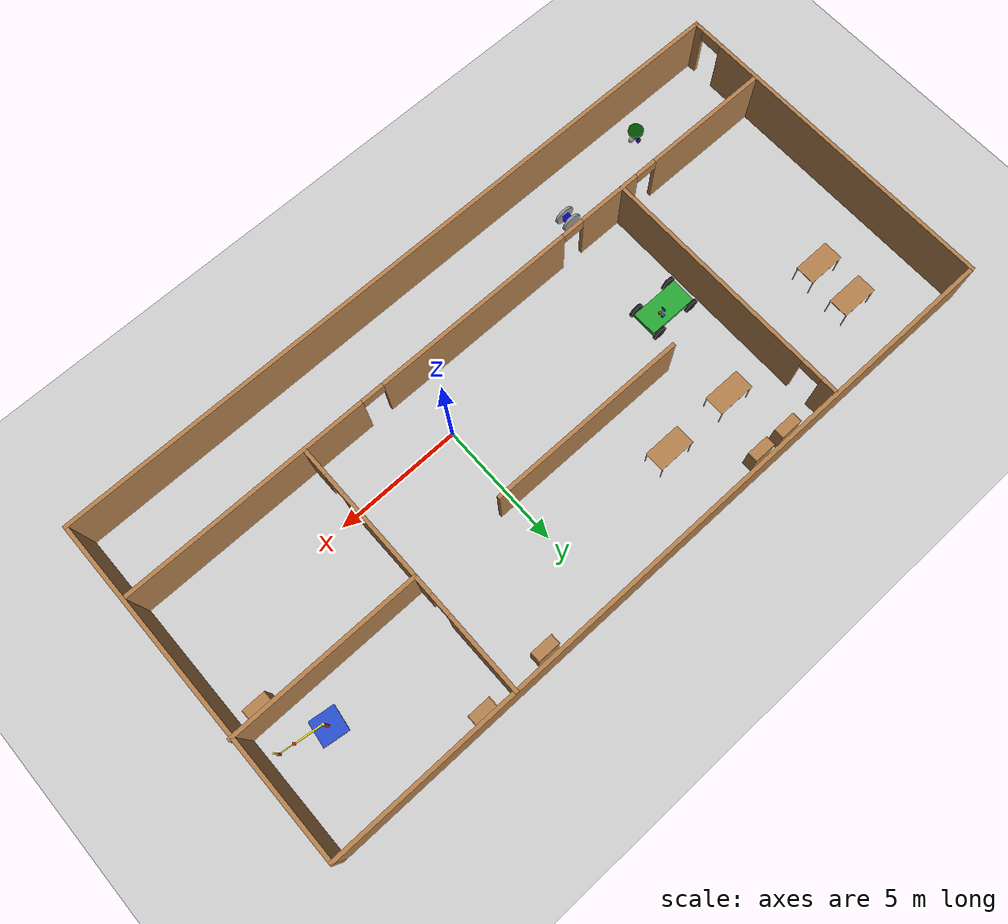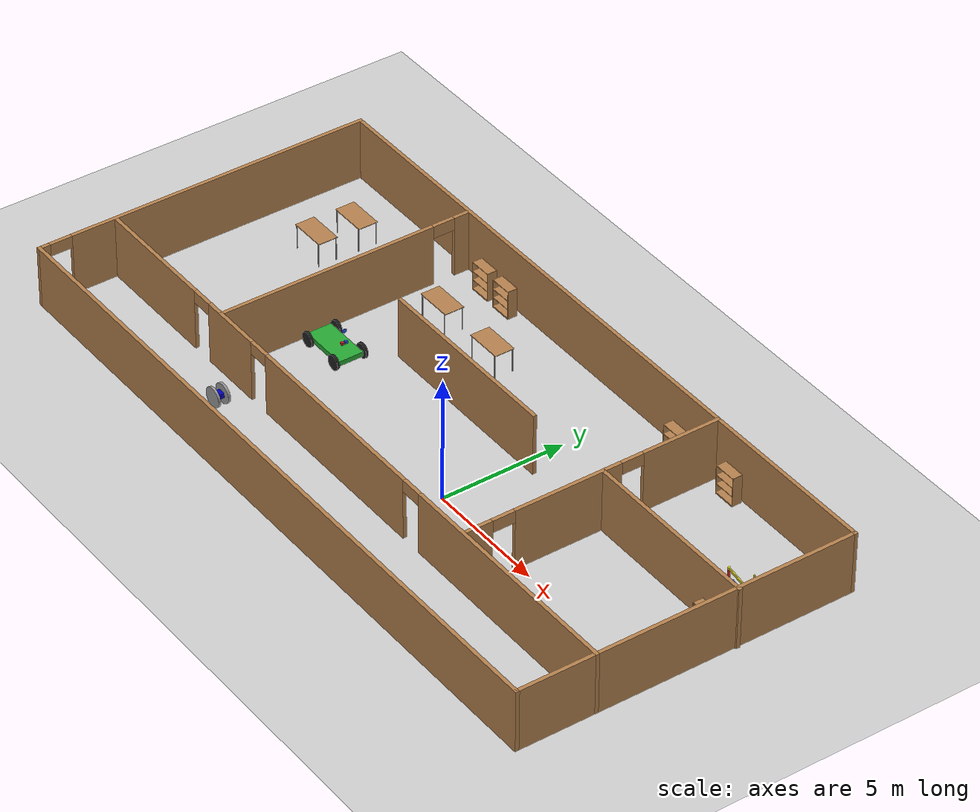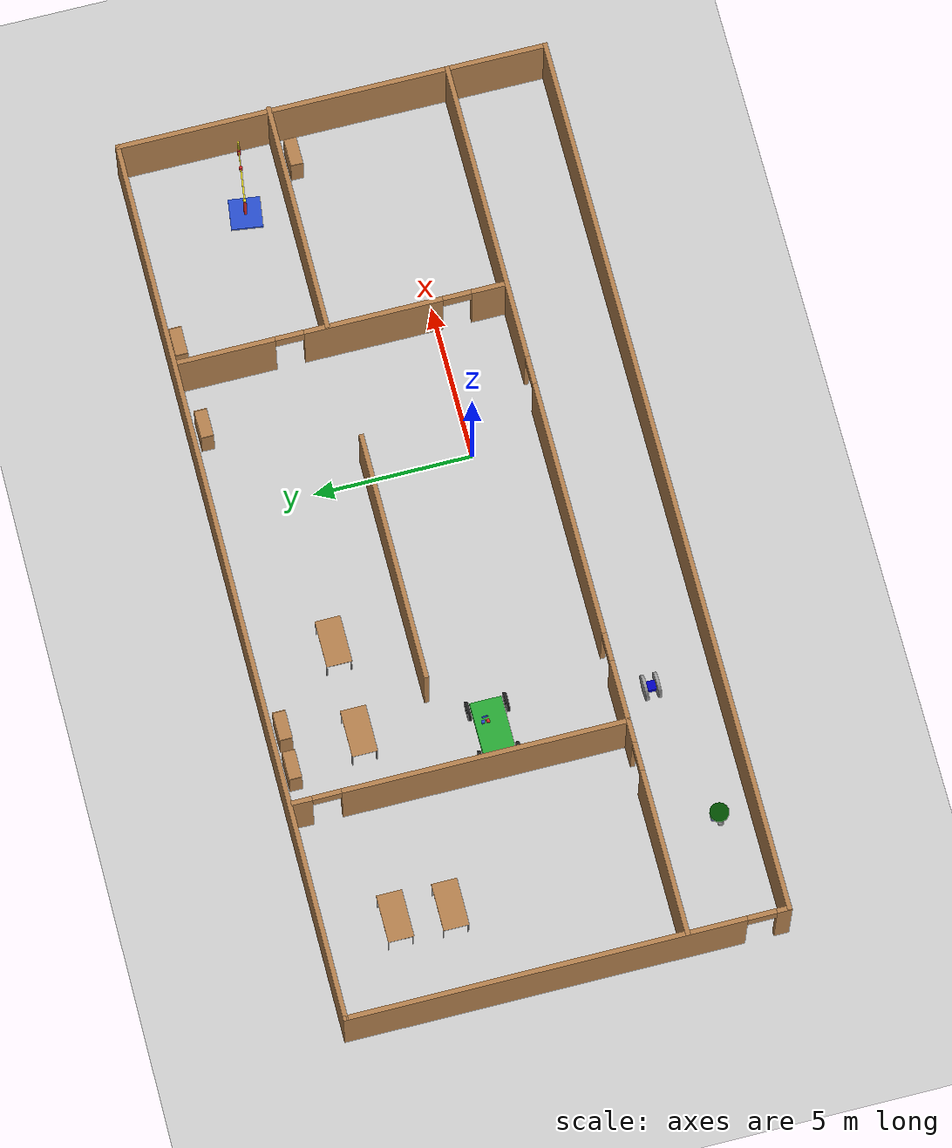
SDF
<sdf version="1.6">
 <world name="default">
  <plugin name="hello" filename="libhello.so"/>
  <light name="sun" type="directional">
   <pose>0 0 10 0 -0 0</pose>
   <diffuse>0.8 0.8 0.8 1</diffuse>
   <specular>0.2 0.2 0.2 1</specular>
   <attenuation>
    <range>1000</range>
    <constant>0.9</constant>
    <linear>0.01</linear>
    <quadratic>0.001</quadratic>
   </attenuation>
   <direction>-0.5 0.1 -0.9</direction>
  </light>
  <model name="ground_plane">
   <static>1</static>
   <link name="link">
    <collision name="collision">
     <geometry><plane><normal>0 0 1</normal><size>100 100</size></plane></geometry>
     <surface>
      <contact><collide_bitmask>65535</collide_bitmask></contact>
      <friction><ode><mu>100</mu><mu2>50</mu2></ode></friction>
     </surface>
    </collision>
    <visual name="visual">
     <cast_shadows>0</cast_shadows>
     <geometry><plane><normal>0 0 1</normal><size>100 100</size></plane></geometry>
     <material>
      <script><uri>file://media/materials/scripts/gazebo.material</uri><name>Gazebo/Grey</name></script>
     </material>
    </visual>
   </link>
  </model>
  <gravity>0 0 -9.8</gravity>
  <magnetic_field>6e-06 2.3e-05 -4.2e-05</magnetic_field>
  <atmosphere type="adiabatic"/>
  <physics name="default_physics" default="0" type="ode">
   <max_step_size>0.001</max_step_size>
   <real_time_factor>1</real_time_factor>
   <real_time_update_rate>1000</real_time_update_rate>
  </physics>
  <scene><ambient>0.4 0.4 0.4 1</ambient><background>0.7 0.7 0.7 1</background><shadows>1</shadows></scene>
  <spherical_coordinates>
   <surface_model>EARTH_WGS84</surface_model>
   <latitude_deg>0</latitude_deg>
   <longitude_deg>0</longitude_deg>
   <elevation>0</elevation>
   <heading_deg>0</heading_deg>
  </spherical_coordinates>
  <model name="bookshelf">
   <static>1</static>
   <link name="link">
    <inertial><mass>1</mass></inertial>
    <collision name="back">
     <pose>0 0.005 0.6 0 -0 0</pose>
     <geometry><box><size>0.9 0.01 1.2</size></box></geometry>
    </collision>
    <visual name="visual1">
     <pose>0 0.005 0.6 0 -0 0</pose>
     <geometry><box><size>0.9 0.01 1.2</size></box></geometry>
     <material>
      <script><uri>file://media/materials/scripts/gazebo.material</uri><name>Gazebo/Wood</name></script>
     </material>
    </visual>
    <collision name="left_side">
     <pose>0.45 -0.195 0.6 0 -0 0</pose>
     <geometry><box><size>0.02 0.4 1.2</size></box></geometry>
    </collision>
    <visual name="visual2">
     <pose>0.45 -0.195 0.6 0 -0 0</pose>
     <geometry><box><size>0.02 0.4 1.2</size></box></geometry>
     <material>
      <script><uri>file://media/materials/scripts/gazebo.material</uri><name>Gazebo/Wood</name></script>
     </material>
    </visual>
    <collision name="right_side">
     <pose>-0.45 -0.195 0.6 0 -0 0</pose>
     <geometry><box><size>0.02 0.4 1.2</size></box></geometry>
    </collision>
    <visual name="visual3">
     <pose>-0.45 -0.195 0.6 0 -0 0</pose>
     <geometry><box><size>0.02 0.4 1.2</size></box></geometry>
     <material>
      <script><uri>file://media/materials/scripts/gazebo.material</uri><name>Gazebo/Wood</name></script>
     </material>
    </visual>
    <collision name="bottom">
     <pose>0 -0.195 0.03 0 -0 0</pose>
     <geometry><box><size>0.88 0.4 0.06</size></box></geometry>
    </collision>
    <visual name="visual4">
     <pose>0 -0.195 0.03 0 -0 0</pose>
     <geometry><box><size>0.88 0.4 0.06</size></box></geometry>
     <material>
      <script><uri>file://media/materials/scripts/gazebo.material</uri><name>Gazebo/Wood</name></script>
     </material>
    </visual>
    <collision name="top">
     <pose>0 -0.195 1.19 0 -0 0</pose>
     <geometry><box><size>0.88 0.4 0.02</size></box></geometry>
    </collision>
    <visual name="visual5">
     <pose>0 -0.195 1.19 0 -0 0</pose>
     <geometry><box><size>0.88 0.4 0.02</size></box></geometry>
     <material>
      <script><uri>file://media/materials/scripts/gazebo.material</uri><name>Gazebo/Wood</name></script>
     </material>
    </visual>
    <collision name="low_shelf">
     <pose>0 -0.195 0.43 0 -0 0</pose>
     <geometry><box><size>0.88 0.4 0.02</size></box></geometry>
    </collision>
    <visual name="visual6">
     <pose>0 -0.195 0.43 0 -0 0</pose>
     <geometry><box><size>0.88 0.4 0.02</size></box></geometry>
     <material>
      <script><uri>file://media/materials/scripts/gazebo.material</uri><name>Gazebo/Wood</name></script>
     </material>
    </visual>
    <collision name="high_shelf">
     <pose>0 -0.195 0.8 0 -0 0</pose>
     <geometry><box><size>0.88 0.4 0.02</size></box></geometry>
    </collision>
    <visual name="visual7">
     <pose>0 -0.195 0.8 0 -0 0</pose>
     <geometry><box><size>0.88 0.4 0.02</size></box></geometry>
     <material>
      <script><uri>file://media/materials/scripts/gazebo.material</uri><name>Gazebo/Wood</name></script>
     </material>
    </visual>
   </link>
   <pose>-8.56242 8.01045 0 0 -0 0</pose>
  </model>
  <model name="bookshelf_0">
   <static>1</static>
   <link name="link">
    <inertial><mass>1</mass></inertial>
    <collision name="back">
     <pose>0 0.005 0.6 0 -0 0</pose>
     <geometry><box><size>0.9 0.01 1.2</size></box></geometry>
    </collision>
    <visual name="visual1">
     <pose>0 0.005 0.6 0 -0 0</pose>
     <geometry><box><size>0.9 0.01 1.2</size></box></geometry>
     <material>
      <script><uri>file://media/materials/scripts/gazebo.material</uri><name>Gazebo/Wood</name></script>
     </material>
    </visual>
    <collision name="left_side">
     <pose>0.45 -0.195 0.6 0 -0 0</pose>
     <geometry><box><size>0.02 0.4 1.2</size></box></geometry>
    </collision>
    <visual name="visual2">
     <pose>0.45 -0.195 0.6 0 -0 0</pose>
     <geometry><box><size>0.02 0.4 1.2</size></box></geometry>
     <material>
      <script><uri>file://media/materials/scripts/gazebo.material</uri><name>Gazebo/Wood</name></script>
     </material>
    </visual>
    <collision name="right_side">
     <pose>-0.45 -0.195 0.6 0 -0 0</pose>
     <geometry><box><size>0.02 0.4 1.2</size></box></geometry>
    </collision>
    <visual name="visual3">
     <pose>-0.45 -0.195 0.6 0 -0 0</pose>
     <geometry><box><size>0.02 0.4 1.2</size></box></geometry>
     <material>
      <script><uri>file://media/materials/scripts/gazebo.material</uri><name>Gazebo/Wood</name></script>
     </material>
    </visual>
    <collision name="bottom">
     <pose>0 -0.195 0.03 0 -0 0</pose>
     <geometry><box><size>0.88 0.4 0.06</size></box></geometry>
    </collision>
    <visual name="visual4">
     <pose>0 -0.195 0.03 0 -0 0</pose>
     <geometry><box><size>0.88 0.4 0.06</size></box></geometry>
     <material>
      <script><uri>file://media/materials/scripts/gazebo.material</uri><name>Gazebo/Wood</name></script>
     </material>
    </visual>
    <collision name="top">
     <pose>0 -0.195 1.19 0 -0 0</pose>
     <geometry><box><size>0.88 0.4 0.02</size></box></geometry>
    </collision>
    <visual name="visual5">
     <pose>0 -0.195 1.19 0 -0 0</pose>
     <geometry><box><size>0.88 0.4 0.02</size></box></geometry>
     <material>
      <script><uri>file://media/materials/scripts/gazebo.material</uri><name>Gazebo/Wood</name></script>
     </material>
    </visual>
    <collision name="low_shelf">
     <pose>0 -0.195 0.43 0 -0 0</pose>
     <geometry><box><size>0.88 0.4 0.02</size></box></geometry>
    </collision>
    <visual name="visual6">
     <pose>0 -0.195 0.43 0 -0 0</pose>
     <geometry><box><size>0.88 0.4 0.02</size></box></geometry>
     <material>
      <script><uri>file://media/materials/scripts/gazebo.material</uri><name>Gazebo/Wood</name></script>
     </material>
    </visual>
    <collision name="high_shelf">
     <pose>0 -0.195 0.8 0 -0 0</pose>
     <geometry><box><size>0.88 0.4 0.02</size></box></geometry>
    </collision>
    <visual name="visual7">
     <pose>0 -0.195 0.8 0 -0 0</pose>
     <geometry><box><size>0.88 0.4 0.02</size></box></geometry>
     <material>
      <script><uri>file://media/materials/scripts/gazebo.material</uri><name>Gazebo/Wood</name></script>
     </material>
    </visual>
   </link>
   <pose>-7.2922 7.98947 0 0 -0 0</pose>
  </model>
  <model name="bookshelf_1">
   <static>1</static>
   <link name="link">
    <inertial><mass>1</mass></inertial>
    <collision name="back">
     <pose>0 0.005 0.6 0 -0 0</pose>
     <geometry><box><size>0.9 0.01 1.2</size></box></geometry>
    </collision>
    <visual name="visual1">
     <pose>0 0.005 0.6 0 -0 0</pose>
     <geometry><box><size>0.9 0.01 1.2</size></box></geometry>
     <material>
      <script><uri>file://media/materials/scripts/gazebo.material</uri><name>Gazebo/Wood</name></script>
     </material>
    </visual>
    <collision name="left_side">
     <pose>0.45 -0.195 0.6 0 -0 0</pose>
     <geometry><box><size>0.02 0.4 1.2</size></box></geometry>
    </collision>
    <visual name="visual2">
     <pose>0.45 -0.195 0.6 0 -0 0</pose>
     <geometry><box><size>0.02 0.4 1.2</size></box></geometry>
     <material>
      <script><uri>file://media/materials/scripts/gazebo.material</uri><name>Gazebo/Wood</name></script>
     </material>
    </visual>
    <collision name="right_side">
     <pose>-0.45 -0.195 0.6 0 -0 0</pose>
     <geometry><box><size>0.02 0.4 1.2</size></box></geometry>
    </collision>
    <visual name="visual3">
     <pose>-0.45 -0.195 0.6 0 -0 0</pose>
     <geometry><box><size>0.02 0.4 1.2</size></box></geometry>
     <material>
      <script><uri>file://media/materials/scripts/gazebo.material</uri><name>Gazebo/Wood</name></script>
     </material>
    </visual>
    <collision name="bottom">
     <pose>0 -0.195 0.03 0 -0 0</pose>
     <geometry><box><size>0.88 0.4 0.06</size></box></geometry>
    </collision>
    <visual name="visual4">
     <pose>0 -0.195 0.03 0 -0 0</pose>
     <geometry><box><size>0.88 0.4 0.06</size></box></geometry>
     <material>
      <script><uri>file://media/materials/scripts/gazebo.material</uri><name>Gazebo/Wood</name></script>
     </material>
    </visual>
    <collision name="top">
     <pose>0 -0.195 1.19 0 -0 0</pose>
     <geometry><box><size>0.88 0.4 0.02</size></box></geometry>
    </collision>
    <visual name="visual5">
     <pose>0 -0.195 1.19 0 -0 0</pose>
     <geometry><box><size>0.88 0.4 0.02</size></box></geometry>
     <material>
      <script><uri>file://media/materials/scripts/gazebo.material</uri><name>Gazebo/Wood</name></script>
     </material>
    </visual>
    <collision name="low_shelf">
     <pose>0 -0.195 0.43 0 -0 0</pose>
     <geometry><box><size>0.88 0.4 0.02</size></box></geometry>
    </collision>
    <visual name="visual6">
     <pose>0 -0.195 0.43 0 -0 0</pose>
     <geometry><box><size>0.88 0.4 0.02</size></box></geometry>
     <material>
      <script><uri>file://media/materials/scripts/gazebo.material</uri><name>Gazebo/Wood</name></script>
     </material>
    </visual>
    <collision name="high_shelf">
     <pose>0 -0.195 0.8 0 -0 0</pose>
     <geometry><box><size>0.88 0.4 0.02</size></box></geometry>
    </collision>
    <visual name="visual7">
     <pose>0 -0.195 0.8 0 -0 0</pose>
     <geometry><box><size>0.88 0.4 0.02</size></box></geometry>
     <material>
      <script><uri>file://media/materials/scripts/gazebo.material</uri><name>Gazebo/Wood</name></script>
     </material>
    </visual>
   </link>
   <pose>2.68277 7.97462 0 0 -0 0</pose>
  </model>
  <model name="table">
   <static>1</static>
   <link name="link">
    <collision name="surface">
     <pose>0 0 1 0 -0 0</pose>
     <geometry><box><size>1.5 0.8 0.03</size></box></geometry>
     <surface><friction><ode><mu>0.6</mu><mu2>0.6</mu2></ode></friction></surface>
    </collision>
    <visual name="visual1">
     <pose>0 0 1 0 -0 0</pose>
     <geometry><box><size>1.5 0.8 0.03</size></box></geometry>
     <material>
      <script><uri>file://media/materials/scripts/gazebo.material</uri><name>Gazebo/Wood</name></script>
     </material>
    </visual>
    <collision name="front_left_leg">
     <pose>0.68 0.38 0.5 0 -0 0</pose>
     <geometry><cylinder><radius>0.02</radius><length>1</length></cylinder></geometry>
    </collision>
    <visual name="front_left_leg">
     <pose>0.68 0.38 0.5 0 -0 0</pose>
     <geometry><cylinder><radius>0.02</radius><length>1</length></cylinder></geometry>
     <material>
      <script><uri>file://media/materials/scripts/gazebo.material</uri><name>Gazebo/Grey</name></script>
     </material>
    </visual>
    <collision name="front_right_leg">
     <pose>0.68 -0.38 0.5 0 -0 0</pose>
     <geometry><cylinder><radius>0.02</radius><length>1</length></cylinder></geometry>
    </collision>
    <visual name="front_right_leg">
     <pose>0.68 -0.38 0.5 0 -0 0</pose>
     <geometry><cylinder><radius>0.02</radius><length>1</length></cylinder></geometry>
     <material>
      <script><uri>file://media/materials/scripts/gazebo.material</uri><name>Gazebo/Grey</name></script>
     </material>
    </visual>
    <collision name="back_right_leg">
     <pose>-0.68 -0.38 0.5 0 -0 0</pose>
     <geometry><cylinder><radius>0.02</radius><length>1</length></cylinder></geometry>
    </collision>
    <visual name="back_right_leg">
     <pose>-0.68 -0.38 0.5 0 -0 0</pose>
     <geometry><cylinder><radius>0.02</radius><length>1</length></cylinder></geometry>
     <material>
      <script><uri>file://media/materials/scripts/gazebo.material</uri><name>Gazebo/Grey</name></script>
     </material>
    </visual>
    <collision name="back_left_leg">
     <pose>-0.68 0.38 0.5 0 -0 0</pose>
     <geometry><cylinder><radius>0.02</radius><length>1</length></cylinder></geometry>
    </collision>
    <visual name="back_left_leg">
     <pose>-0.68 0.38 0.5 0 -0 0</pose>
     <geometry><cylinder><radius>0.02</radius><length>1</length></cylinder></geometry>
     <material>
      <script><uri>file://media/materials/scripts/gazebo.material</uri><name>Gazebo/Grey</name></script>
     </material>
    </visual>
   </link>
   <pose>-13.8712 5.96669 0 0 -0 0</pose>
  </model>
  <model name="table_0">
   <static>1</static>
   <link name="link">
    <collision name="surface">
     <pose>0 0 1 0 -0 0</pose>
     <geometry><box><size>1.5 0.8 0.03</size></box></geometry>
     <surface><friction><ode><mu>0.6</mu><mu2>0.6</mu2></ode></friction></surface>
    </collision>
    <visual name="visual1">
     <pose>0 0 1 0 -0 0</pose>
     <geometry><box><size>1.5 0.8 0.03</size></box></geometry>
     <material>
      <script><uri>file://media/materials/scripts/gazebo.material</uri><name>Gazebo/Wood</name></script>
     </material>
    </visual>
    <collision name="front_left_leg">
     <pose>0.68 0.38 0.5 0 -0 0</pose>
     <geometry><cylinder><radius>0.02</radius><length>1</length></cylinder></geometry>
    </collision>
    <visual name="front_left_leg">
     <pose>0.68 0.38 0.5 0 -0 0</pose>
     <geometry><cylinder><radius>0.02</radius><length>1</length></cylinder></geometry>
     <material>
      <script><uri>file://media/materials/scripts/gazebo.material</uri><name>Gazebo/Grey</name></script>
     </material>
    </visual>
    <collision name="front_right_leg">
     <pose>0.68 -0.38 0.5 0 -0 0</pose>
     <geometry><cylinder><radius>0.02</radius><length>1</length></cylinder></geometry>
    </collision>
    <visual name="front_right_leg">
     <pose>0.68 -0.38 0.5 0 -0 0</pose>
     <geometry><cylinder><radius>0.02</radius><length>1</length></cylinder></geometry>
     <material>
      <script><uri>file://media/materials/scripts/gazebo.material</uri><name>Gazebo/Grey</name></script>
     </material>
    </visual>
    <collision name="back_right_leg">
     <pose>-0.68 -0.38 0.5 0 -0 0</pose>
     <geometry><cylinder><radius>0.02</radius><length>1</length></cylinder></geometry>
    </collision>
    <visual name="back_right_leg">
     <pose>-0.68 -0.38 0.5 0 -0 0</pose>
     <geometry><cylinder><radius>0.02</radius><length>1</length></cylinder></geometry>
     <material>
      <script><uri>file://media/materials/scripts/gazebo.material</uri><name>Gazebo/Grey</name></script>
     </material>
    </visual>
    <collision name="back_left_leg">
     <pose>-0.68 0.38 0.5 0 -0 0</pose>
     <geometry><cylinder><radius>0.02</radius><length>1</length></cylinder></geometry>
    </collision>
    <visual name="back_left_leg">
     <pose>-0.68 0.38 0.5 0 -0 0</pose>
     <geometry><cylinder><radius>0.02</radius><length>1</length></cylinder></geometry>
     <material>
      <script><uri>file://media/materials/scripts/gazebo.material</uri><name>Gazebo/Grey</name></script>
     </material>
    </visual>
   </link>
   <pose>-13.9294 4.27965 0 0 -0 0</pose>
  </model>
  <model name="table_1">
   <static>1</static>
   <link name="link">
    <collision name="surface">
     <pose>0 0 1 0 -0 0</pose>
     <geometry><box><size>1.5 0.8 0.03</size></box></geometry>
     <surface><friction><ode><mu>0.6</mu><mu2>0.6</mu2></ode></friction></surface>
    </collision>
    <visual name="visual1">
     <pose>0 0 1 0 -0 0</pose>
     <geometry><box><size>1.5 0.8 0.03</size></box></geometry>
     <material>
      <script><uri>file://media/materials/scripts/gazebo.material</uri><name>Gazebo/Wood</name></script>
     </material>
    </visual>
    <collision name="front_left_leg">
     <pose>0.68 0.38 0.5 0 -0 0</pose>
     <geometry><cylinder><radius>0.02</radius><length>1</length></cylinder></geometry>
    </collision>
    <visual name="front_left_leg">
     <pose>0.68 0.38 0.5 0 -0 0</pose>
     <geometry><cylinder><radius>0.02</radius><length>1</length></cylinder></geometry>
     <material>
      <script><uri>file://media/materials/scripts/gazebo.material</uri><name>Gazebo/Grey</name></script>
     </material>
    </visual>
    <collision name="front_right_leg">
     <pose>0.68 -0.38 0.5 0 -0 0</pose>
     <geometry><cylinder><radius>0.02</radius><length>1</length></cylinder></geometry>
    </collision>
    <visual name="front_right_leg">
     <pose>0.68 -0.38 0.5 0 -0 0</pose>
     <geometry><cylinder><radius>0.02</radius><length>1</length></cylinder></geometry>
     <material>
      <script><uri>file://media/materials/scripts/gazebo.material</uri><name>Gazebo/Grey</name></script>
     </material>
    </visual>
    <collision name="back_right_leg">
     <pose>-0.68 -0.38 0.5 0 -0 0</pose>
     <geometry><cylinder><radius>0.02</radius><length>1</length></cylinder></geometry>
    </collision>
    <visual name="back_right_leg">
     <pose>-0.68 -0.38 0.5 0 -0 0</pose>
     <geometry><cylinder><radius>0.02</radius><length>1</length></cylinder></geometry>
     <material>
      <script><uri>file://media/materials/scripts/gazebo.material</uri><name>Gazebo/Grey</name></script>
     </material>
    </visual>
    <collision name="back_left_leg">
     <pose>-0.68 0.38 0.5 0 -0 0</pose>
     <geometry><cylinder><radius>0.02</radius><length>1</length></cylinder></geometry>
    </collision>
    <visual name="back_left_leg">
     <pose>-0.68 0.38 0.5 0 -0 0</pose>
     <geometry><cylinder><radius>0.02</radius><length>1</length></cylinder></geometry>
     <material>
      <script><uri>file://media/materials/scripts/gazebo.material</uri><name>Gazebo/Grey</name></script>
     </material>
    </visual>
   </link>
   <pose>-5.04097 5.64271 0 0 -0 0</pose>
  </model>
  <model name="table_2">
   <static>1</static>
   <link name="link">
    <collision name="surface">
     <pose>0 0 1 0 -0 0</pose>
     <geometry><box><size>1.5 0.8 0.03</size></box></geometry>
     <surface><friction><ode><mu>0.6</mu><mu2>0.6</mu2></ode></friction></surface>
    </collision>
    <visual name="visual1">
     <pose>0 0 1 0 -0 0</pose>
     <geometry><box><size>1.5 0.8 0.03</size></box></geometry>
     <material>
      <script><uri>file://media/materials/scripts/gazebo.material</uri><name>Gazebo/Wood</name></script>
     </material>
    </visual>
    <collision name="front_left_leg">
     <pose>0.68 0.38 0.5 0 -0 0</pose>
     <geometry><cylinder><radius>0.02</radius><length>1</length></cylinder></geometry>
    </collision>
    <visual name="front_left_leg">
     <pose>0.68 0.38 0.5 0 -0 0</pose>
     <geometry><cylinder><radius>0.02</radius><length>1</length></cylinder></geometry>
     <material>
      <script><uri>file://media/materials/scripts/gazebo.material</uri><name>Gazebo/Grey</name></script>
     </material>
    </visual>
    <collision name="front_right_leg">
     <pose>0.68 -0.38 0.5 0 -0 0</pose>
     <geometry><cylinder><radius>0.02</radius><length>1</length></cylinder></geometry>
    </collision>
    <visual name="front_right_leg">
     <pose>0.68 -0.38 0.5 0 -0 0</pose>
     <geometry><cylinder><radius>0.02</radius><length>1</length></cylinder></geometry>
     <material>
      <script><uri>file://media/materials/scripts/gazebo.material</uri><name>Gazebo/Grey</name></script>
     </material>
    </visual>
    <collision name="back_right_leg">
     <pose>-0.68 -0.38 0.5 0 -0 0</pose>
     <geometry><cylinder><radius>0.02</radius><length>1</length></cylinder></geometry>
    </collision>
    <visual name="back_right_leg">
     <pose>-0.68 -0.38 0.5 0 -0 0</pose>
     <geometry><cylinder><radius>0.02</radius><length>1</length></cylinder></geometry>
     <material>
      <script><uri>file://media/materials/scripts/gazebo.material</uri><name>Gazebo/Grey</name></script>
     </material>
    </visual>
    <collision name="back_left_leg">
     <pose>-0.68 0.38 0.5 0 -0 0</pose>
     <geometry><cylinder><radius>0.02</radius><length>1</length></cylinder></geometry>
    </collision>
    <visual name="back_left_leg">
     <pose>-0.68 0.38 0.5 0 -0 0</pose>
     <geometry><cylinder><radius>0.02</radius><length>1</length></cylinder></geometry>
     <material>
      <script><uri>file://media/materials/scripts/gazebo.material</uri><name>Gazebo/Grey</name></script>
     </material>
    </visual>
   </link>
   <pose>-7.98228 5.59007 0 0 -0 0</pose>
  </model>
  <model name="car">
   <link name="chassis">
    <pose>0 0 0.3 0 -0 0</pose>
    <collision name="collision"><geometry><box><size>2 1 0.2</size></box></geometry></collision>
    <visual name="visual">
     <geometry><box><size>2 1 0.2</size></box></geometry>
     <material>
      <script><uri>file://media/materials/scripts/gazebo.material</uri><name>Gazebo/Green</name></script>
     </material>
    </visual>
    <inertial>
     <inertia><ixx>1</ixx><ixy>0</ixy><ixz>0</ixz><iyy>1</iyy><iyz>0</iyz><izz>1</izz></inertia>
     <mass>1</mass>
    </inertial>
   </link>
   <link name="front_left_wheel">
    <pose>0.8 0.6 0.3 -0 1.5707 1.5707</pose>
    <collision name="collision">
     <geometry><cylinder><radius>0.3</radius><length>0.1</length></cylinder></geometry>
    </collision>
    <visual name="visual">
     <geometry><cylinder><radius>0.3</radius><length>0.1</length></cylinder></geometry>
     <material>
      <script><uri>file://media/materials/scripts/gazebo.material</uri><name>Gazebo/Black</name></script>
     </material>
    </visual>
    <inertial>
     <inertia><ixx>1</ixx><ixy>0</ixy><ixz>0</ixz><iyy>1</iyy><iyz>0</iyz><izz>1</izz></inertia>
     <mass>1</mass>
    </inertial>
   </link>
   <link name="front_right_wheel">
    <pose>0.8 -0.6 0.3 -0 1.5707 1.5707</pose>
    <collision name="collision">
     <geometry><cylinder><radius>0.3</radius><length>0.1</length></cylinder></geometry>
    </collision>
    <visual name="visual">
     <geometry><cylinder><radius>0.3</radius><length>0.1</length></cylinder></geometry>
     <material>
      <script><uri>file://media/materials/scripts/gazebo.material</uri><name>Gazebo/Black</name></script>
     </material>
    </visual>
    <inertial>
     <inertia><ixx>1</ixx><ixy>0</ixy><ixz>0</ixz><iyy>1</iyy><iyz>0</iyz><izz>1</izz></inertia>
     <mass>1</mass>
    </inertial>
   </link>
   <link name="back_right_wheel">
    <pose>-0.8 -0.6 0.3 -0 1.5707 1.5707</pose>
    <collision name="collision">
     <geometry><cylinder><radius>0.3</radius><length>0.1</length></cylinder></geometry>
    </collision>
    <visual name="visual">
     <geometry><cylinder><radius>0.3</radius><length>0.1</length></cylinder></geometry>
     <material>
      <script><uri>file://media/materials/scripts/gazebo.material</uri><name>Gazebo/Black</name></script>
     </material>
    </visual>
    <inertial>
     <inertia><ixx>1</ixx><ixy>0</ixy><ixz>0</ixz><iyy>1</iyy><iyz>0</iyz><izz>1</izz></inertia>
     <mass>1</mass>
    </inertial>
   </link>
   <link name="back_left_wheel">
    <pose>-0.8 0.6 0.3 -0 1.5707 1.5707</pose>
    <collision name="collision">
     <geometry><cylinder><radius>0.3</radius><length>0.1</length></cylinder></geometry>
    </collision>
    <visual name="visual">
     <geometry><cylinder><radius>0.3</radius><length>0.1</length></cylinder></geometry>
     <material>
      <script><uri>file://media/materials/scripts/gazebo.material</uri><name>Gazebo/Black</name></script>
     </material>
    </visual>
    <inertial>
     <inertia><ixx>1</ixx><ixy>0</ixy><ixz>0</ixz><iyy>1</iyy><iyz>0</iyz><izz>1</izz></inertia>
     <mass>1</mass>
    </inertial>
   </link>
   <link name="gas_pedal">
    <pose>0.3 0.1 0.5 0 -0 0</pose>
    <collision name="collision"><geometry><box><size>0.1 0.1 0.1</size></box></geometry></collision>
    <visual name="visual">
     <geometry><box><size>0.1 0.1 0.1</size></box></geometry>
     <material>
      <script><uri>file://media/materials/scripts/gazebo.material</uri><name>Gazebo/Red</name></script>
     </material>
    </visual>
    <inertial>
     <inertia><ixx>1</ixx><ixy>0</ixy><ixz>0</ixz><iyy>1</iyy><iyz>0</iyz><izz>1</izz></inertia>
     <mass>1</mass>
    </inertial>
   </link>
   <link name="brake_pedal">
    <pose>0.3 0.25 0.5 0 -0 0</pose>
    <collision name="collision"><geometry><box><size>0.1 0.1 0.1</size></box></geometry></collision>
    <visual name="visual">
     <geometry><box><size>0.1 0.1 0.1</size></box></geometry>
     <material>
      <script><uri>file://media/materials/scripts/gazebo.material</uri><name>Gazebo/Blue</name></script>
     </material>
    </visual>
    <inertial>
     <inertia><ixx>1</ixx><ixy>0</ixy><ixz>0</ixz><iyy>1</iyy><iyz>0</iyz><izz>1</izz></inertia>
     <mass>1</mass>
    </inertial>
   </link>
   <link name="steering_wheel">
    <pose>0.3 0.2 1 0 1.5707 0</pose>
    <collision name="collision">
     <geometry><cylinder><radius>0.1</radius><length>0.01</length></cylinder></geometry>
    </collision>
    <visual name="visual">
     <geometry><cylinder><radius>0.1</radius><length>0.01</length></cylinder></geometry>
     <material>
      <script><uri>file://media/materials/scripts/gazebo.material</uri><name>Gazebo/Blue</name></script>
     </material>
    </visual>
    <inertial>
     <inertia><ixx>1</ixx><ixy>0</ixy><ixz>0</ixz><iyy>1</iyy><iyz>0</iyz><izz>1</izz></inertia>
     <mass>1</mass>
    </inertial>
   </link>
   <joint name="gas_joint" type="prismatic">
    <parent>chassis</parent>
    <child>gas_pedal</child>
    <axis>
     <xyz>1 0 0</xyz>
     <limit><lower>0</lower><upper>0.2</upper></limit>
     <use_parent_model_frame>1</use_parent_model_frame>
     <dynamics><spring_reference>0</spring_reference><spring_stiffness>0</spring_stiffness></dynamics>
    </axis>
   </joint>
   <joint name="brake_joint" type="prismatic">
    <parent>chassis</parent>
    <child>brake_pedal</child>
    <axis>
     <xyz>1 0 0</xyz>
     <limit><lower>0</lower><upper>0.2</upper></limit>
     <use_parent_model_frame>1</use_parent_model_frame>
     <dynamics><spring_reference>0</spring_reference><spring_stiffness>0</spring_stiffness></dynamics>
    </axis>
   </joint>
   <joint name="steering_joint" type="revolute">
    <parent>chassis</parent>
    <child>steering_wheel</child>
    <axis>
     <xyz>1 0 0</xyz>
     <limit><lower>-7.853</lower><upper>7.853</upper></limit>
     <use_parent_model_frame>1</use_parent_model_frame>
     <dynamics><spring_reference>0</spring_reference><spring_stiffness>0</spring_stiffness></dynamics>
    </axis>
   </joint>
   <joint name="front_left_joint" type="revolute2">
    <parent>chassis</parent>
    <child>front_left_wheel</child>
    <axis>
     <xyz>0 0 1</xyz>
     <limit><lower>8.6632e-06</lower><upper>8.6632e-06</upper></limit>
     <use_parent_model_frame>1</use_parent_model_frame>
     <dynamics><spring_reference>0</spring_reference><spring_stiffness>0</spring_stiffness></dynamics>
    </axis>
    <axis2>
     <xyz>0 1 0</xyz>
     <use_parent_model_frame>1</use_parent_model_frame>
     <dynamics><spring_reference>0</spring_reference><spring_stiffness>0</spring_stiffness></dynamics>
    </axis2>
    <physics><ode><limit><cfm>0</cfm><erp>0.9</erp></limit></ode></physics>
   </joint>
   <joint name="front_right_joint" type="revolute2">
    <parent>chassis</parent>
    <child>front_right_wheel</child>
    <axis>
     <xyz>0 0 1</xyz>
     <limit><lower>8.6632e-06</lower><upper>8.6632e-06</upper></limit>
     <use_parent_model_frame>1</use_parent_model_frame>
     <dynamics><spring_reference>0</spring_reference><spring_stiffness>0</spring_stiffness></dynamics>
    </axis>
    <axis2>
     <xyz>0 1 0</xyz>
     <use_parent_model_frame>1</use_parent_model_frame>
     <dynamics><spring_reference>0</spring_reference><spring_stiffness>0</spring_stiffness></dynamics>
    </axis2>
    <physics><ode><limit><cfm>0</cfm><erp>0.9</erp></limit></ode></physics>
   </joint>
   <joint name="back_right_joint" type="revolute2">
    <parent>chassis</parent>
    <child>back_right_wheel</child>
    <axis>
     <xyz>0 0 1</xyz>
     <limit><lower>0</lower><upper>0</upper></limit>
     <use_parent_model_frame>1</use_parent_model_frame>
     <dynamics><spring_reference>0</spring_reference><spring_stiffness>0</spring_stiffness></dynamics>
    </axis>
    <axis2>
     <xyz>0 1 0</xyz>
     <use_parent_model_frame>1</use_parent_model_frame>
     <dynamics><spring_reference>0</spring_reference><spring_stiffness>0</spring_stiffness></dynamics>
    </axis2>
    <physics><ode><limit><cfm>0</cfm><erp>0.9</erp></limit></ode></physics>
   </joint>
   <joint name="back_left_joint" type="revolute2">
    <parent>chassis</parent>
    <child>back_left_wheel</child>
    <axis>
     <xyz>0 0 1</xyz>
     <limit><lower>0</lower><upper>0</upper></limit>
     <use_parent_model_frame>1</use_parent_model_frame>
     <dynamics><spring_reference>0</spring_reference><spring_stiffness>0</spring_stiffness></dynamics>
    </axis>
    <axis2>
     <xyz>0 1 0</xyz>
     <use_parent_model_frame>1</use_parent_model_frame>
     <dynamics><spring_reference>0</spring_reference><spring_stiffness>0</spring_stiffness></dynamics>
    </axis2>
    <physics><ode><limit><cfm>0</cfm><erp>0.9</erp></limit></ode></physics>
   </joint>
   <plugin name="vehicle" filename="libVehiclePlugin.so">
    <front_left>front_left_joint</front_left>
    <front_right>front_right_joint</front_right>
    <back_left>back_left_joint</back_left>
    <back_right>back_right_joint</back_right>
    <gas>gas_joint</gas>
    <brake>brake_joint</brake>
    <steering>steering_joint</steering>
    <front_power>10</front_power>
    <rear_power>10</rear_power>
    <tire_angle_range>0.5</tire_angle_range>
    <max_speed>10</max_speed>
    <aero_load>0.1</aero_load>
   </plugin>
   <pose>-8.79204 1.59724 -0.002616 -0.000273 0.000907 0.000875</pose>
  </model>
  <model name="bookshelf_2">
   <static>1</static>
   <link name="link">
    <inertial><mass>1</mass></inertial>
    <collision name="back">
     <pose>0 0.005 0.6 0 -0 0</pose>
     <geometry><box><size>0.9 0.01 1.2</size></box></geometry>
    </collision>
    <visual name="visual1">
     <pose>0 0.005 0.6 0 -0 0</pose>
     <geometry><box><size>0.9 0.01 1.2</size></box></geometry>
     <material>
      <script><uri>file://media/materials/scripts/gazebo.material</uri><name>Gazebo/Wood</name></script>
     </material>
    </visual>
    <collision name="left_side">
     <pose>0.45 -0.195 0.6 0 -0 0</pose>
     <geometry><box><size>0.02 0.4 1.2</size></box></geometry>
    </collision>
    <visual name="visual2">
     <pose>0.45 -0.195 0.6 0 -0 0</pose>
     <geometry><box><size>0.02 0.4 1.2</size></box></geometry>
     <material>
      <script><uri>file://media/materials/scripts/gazebo.material</uri><name>Gazebo/Wood</name></script>
     </material>
    </visual>
    <collision name="right_side">
     <pose>-0.45 -0.195 0.6 0 -0 0</pose>
     <geometry><box><size>0.02 0.4 1.2</size></box></geometry>
    </collision>
    <visual name="visual3">
     <pose>-0.45 -0.195 0.6 0 -0 0</pose>
     <geometry><box><size>0.02 0.4 1.2</size></box></geometry>
     <material>
      <script><uri>file://media/materials/scripts/gazebo.material</uri><name>Gazebo/Wood</name></script>
     </material>
    </visual>
    <collision name="bottom">
     <pose>0 -0.195 0.03 0 -0 0</pose>
     <geometry><box><size>0.88 0.4 0.06</size></box></geometry>
    </collision>
    <visual name="visual4">
     <pose>0 -0.195 0.03 0 -0 0</pose>
     <geometry><box><size>0.88 0.4 0.06</size></box></geometry>
     <material>
      <script><uri>file://media/materials/scripts/gazebo.material</uri><name>Gazebo/Wood</name></script>
     </material>
    </visual>
    <collision name="top">
     <pose>0 -0.195 1.19 0 -0 0</pose>
     <geometry><box><size>0.88 0.4 0.02</size></box></geometry>
    </collision>
    <visual name="visual5">
     <pose>0 -0.195 1.19 0 -0 0</pose>
     <geometry><box><size>0.88 0.4 0.02</size></box></geometry>
     <material>
      <script><uri>file://media/materials/scripts/gazebo.material</uri><name>Gazebo/Wood</name></script>
     </material>
    </visual>
    <collision name="low_shelf">
     <pose>0 -0.195 0.43 0 -0 0</pose>
     <geometry><box><size>0.88 0.4 0.02</size></box></geometry>
    </collision>
    <visual name="visual6">
     <pose>0 -0.195 0.43 0 -0 0</pose>
     <geometry><box><size>0.88 0.4 0.02</size></box></geometry>
     <material>
      <script><uri>file://media/materials/scripts/gazebo.material</uri><name>Gazebo/Wood</name></script>
     </material>
    </visual>
    <collision name="high_shelf">
     <pose>0 -0.195 0.8 0 -0 0</pose>
     <geometry><box><size>0.88 0.4 0.02</size></box></geometry>
    </collision>
    <visual name="visual7">
     <pose>0 -0.195 0.8 0 -0 0</pose>
     <geometry><box><size>0.88 0.4 0.02</size></box></geometry>
     <material>
      <script><uri>file://media/materials/scripts/gazebo.material</uri><name>Gazebo/Wood</name></script>
     </material>
    </visual>
   </link>
   <pose>10.6754 3.15432 0 0 -0 0</pose>
  </model>
  <model name="bookshelf_3">
   <static>1</static>
   <link name="link">
    <inertial><mass>1</mass></inertial>
    <collision name="back">
     <pose>0 0.005 0.6 0 -0 0</pose>
     <geometry><box><size>0.9 0.01 1.2</size></box></geometry>
    </collision>
    <visual name="visual1">
     <pose>0 0.005 0.6 0 -0 0</pose>
     <geometry><box><size>0.9 0.01 1.2</size></box></geometry>
     <material>
      <script><uri>file://media/materials/scripts/gazebo.material</uri><name>Gazebo/Wood</name></script>
     </material>
    </visual>
    <collision name="left_side">
     <pose>0.45 -0.195 0.6 0 -0 0</pose>
     <geometry><box><size>0.02 0.4 1.2</size></box></geometry>
    </collision>
    <visual name="visual2">
     <pose>0.45 -0.195 0.6 0 -0 0</pose>
     <geometry><box><size>0.02 0.4 1.2</size></box></geometry>
     <material>
      <script><uri>file://media/materials/scripts/gazebo.material</uri><name>Gazebo/Wood</name></script>
     </material>
    </visual>
    <collision name="right_side">
     <pose>-0.45 -0.195 0.6 0 -0 0</pose>
     <geometry><box><size>0.02 0.4 1.2</size></box></geometry>
    </collision>
    <visual name="visual3">
     <pose>-0.45 -0.195 0.6 0 -0 0</pose>
     <geometry><box><size>0.02 0.4 1.2</size></box></geometry>
     <material>
      <script><uri>file://media/materials/scripts/gazebo.material</uri><name>Gazebo/Wood</name></script>
     </material>
    </visual>
    <collision name="bottom">
     <pose>0 -0.195 0.03 0 -0 0</pose>
     <geometry><box><size>0.88 0.4 0.06</size></box></geometry>
    </collision>
    <visual name="visual4">
     <pose>0 -0.195 0.03 0 -0 0</pose>
     <geometry><box><size>0.88 0.4 0.06</size></box></geometry>
     <material>
      <script><uri>file://media/materials/scripts/gazebo.material</uri><name>Gazebo/Wood</name></script>
     </material>
    </visual>
    <collision name="top">
     <pose>0 -0.195 1.19 0 -0 0</pose>
     <geometry><box><size>0.88 0.4 0.02</size></box></geometry>
    </collision>
    <visual name="visual5">
     <pose>0 -0.195 1.19 0 -0 0</pose>
     <geometry><box><size>0.88 0.4 0.02</size></box></geometry>
     <material>
      <script><uri>file://media/materials/scripts/gazebo.material</uri><name>Gazebo/Wood</name></script>
     </material>
    </visual>
    <collision name="low_shelf">
     <pose>0 -0.195 0.43 0 -0 0</pose>
     <geometry><box><size>0.88 0.4 0.02</size></box></geometry>
    </collision>
    <visual name="visual6">
     <pose>0 -0.195 0.43 0 -0 0</pose>
     <geometry><box><size>0.88 0.4 0.02</size></box></geometry>
     <material>
      <script><uri>file://media/materials/scripts/gazebo.material</uri><name>Gazebo/Wood</name></script>
     </material>
    </visual>
    <collision name="high_shelf">
     <pose>0 -0.195 0.8 0 -0 0</pose>
     <geometry><box><size>0.88 0.4 0.02</size></box></geometry>
    </collision>
    <visual name="visual7">
     <pose>0 -0.195 0.8 0 -0 0</pose>
     <geometry><box><size>0.88 0.4 0.02</size></box></geometry>
     <material>
      <script><uri>file://media/materials/scripts/gazebo.material</uri><name>Gazebo/Wood</name></script>
     </material>
    </visual>
   </link>
   <pose>5.47958 8.09566 0 0 -0 0</pose>
  </model>
  <model name="simple_arm">
   <link name="arm_base">
    <inertial>
     <pose>0 0 0.00099 0 -0 0</pose>
     <inertia><ixx>1.11</ixx><ixy>0</ixy><ixz>0</ixz><iyy>100.11</iyy><iyz>0</iyz><izz>1.01</izz></inertia>
     <mass>101</mass>
    </inertial>
    <collision name="arm_base_geom">
     <pose>0 0 0.05 0 -0 0</pose>
     <geometry><box><size>1 1 0.1</size></box></geometry>
    </collision>
    <visual name="arm_base_geom_visual">
     <pose>0 0 0.05 0 -0 0</pose>
     <geometry><box><size>1 1 0.1</size></box></geometry>
     <material>
      <script><uri>file://media/materials/scripts/gazebo.material</uri><name>Gazebo/Blue</name></script>
     </material>
    </visual>
    <collision name="arm_base_geom_arm_trunk">
     <pose>0 0 0.6 0 -0 0</pose>
     <geometry><cylinder><radius>0.05</radius><length>1</length></cylinder></geometry>
    </collision>
    <visual name="arm_base_geom_arm_trunk_visual">
     <pose>0 0 0.6 0 -0 0</pose>
     <geometry><cylinder><radius>0.05</radius><length>1</length></cylinder></geometry>
     <material>
      <script><uri>file://media/materials/scripts/gazebo.material</uri><name>Gazebo/Red</name></script>
     </material>
    </visual>
   </link>
   <link name="arm_shoulder_pan">
    <pose>0 0 1.1 0 -0 0</pose>
    <inertial>
     <pose>0.045455 0 0 0 -0 0</pose>
     <inertia><ixx>0.011</ixx><ixy>0</ixy><ixz>0</ixz><iyy>0.0225</iyy><iyz>0</iyz><izz>0.0135</izz></inertia>
     <mass>1.1</mass>
    </inertial>
    <collision name="arm_shoulder_pan_geom">
     <pose>0 0 0.05 0 -0 0</pose>
     <geometry><cylinder><radius>0.05</radius><length>0.1</length></cylinder></geometry>
    </collision>
    <visual name="arm_shoulder_pan_geom_visual">
     <pose>0 0 0.05 0 -0 0</pose>
     <geometry><cylinder><radius>0.05</radius><length>0.1</length></cylinder></geometry>
     <material>
      <script><uri>file://media/materials/scripts/gazebo.material</uri><name>Gazebo/Yellow</name></script>
     </material>
    </visual>
    <collision name="arm_shoulder_pan_geom_arm_shoulder">
     <pose>0.55 0 0.05 0 -0 0</pose>
     <geometry><box><size>1 0.05 0.1</size></box></geometry>
    </collision>
    <visual name="arm_shoulder_pan_geom_arm_shoulder_visual">
     <pose>0.55 0 0.05 0 -0 0</pose>
     <geometry><box><size>1 0.05 0.1</size></box></geometry>
     <material>
      <script><uri>file://media/materials/scripts/gazebo.material</uri><name>Gazebo/Yellow</name></script>
     </material>
    </visual>
   </link>
   <link name="arm_elbow_pan">
    <pose>1.05 0 1.1 0 -0 0</pose>
    <inertial>
     <pose>0.0875 0 0.083333 0 -0 0</pose>
     <inertia>
      <ixx>0.031</ixx>
      <ixy>0</ixy>
      <ixz>0.005</ixz>
      <iyy>0.07275</iyy>
      <iyz>0</iyz>
      <izz>0.04475</izz>
     </inertia>
     <mass>1.2</mass>
    </inertial>
    <collision name="arm_elbow_pan_geom">
     <pose>0 0 0.1 0 -0 0</pose>
     <geometry><cylinder><radius>0.05</radius><length>0.2</length></cylinder></geometry>
    </collision>
    <visual name="arm_elbow_pan_geom_visual">
     <pose>0 0 0.1 0 -0 0</pose>
     <geometry><cylinder><radius>0.05</radius><length>0.2</length></cylinder></geometry>
     <material>
      <script><uri>file://media/materials/scripts/gazebo.material</uri><name>Gazebo/Red</name></script>
     </material>
    </visual>
    <collision name="arm_elbow_pan_geom_arm_elbow">
     <pose>0.3 0 0.15 0 -0 0</pose>
     <geometry><box><size>0.5 0.03 0.1</size></box></geometry>
    </collision>
    <visual name="arm_elbow_pan_geom_arm_elbow_visual">
     <pose>0.3 0 0.15 0 -0 0</pose>
     <geometry><box><size>0.5 0.03 0.1</size></box></geometry>
     <material>
      <script><uri>file://media/materials/scripts/gazebo.material</uri><name>Gazebo/Yellow</name></script>
     </material>
    </visual>
    <collision name="arm_elbow_pan_geom_arm_wrist">
     <pose>0.55 0 0.15 0 -0 0</pose>
     <geometry><cylinder><radius>0.05</radius><length>0.3</length></cylinder></geometry>
    </collision>
    <visual name="arm_elbow_pan_geom_arm_wrist_visual">
     <pose>0.55 0 0.15 0 -0 0</pose>
     <geometry><cylinder><radius>0.05</radius><length>0.3</length></cylinder></geometry>
     <material>
      <script><uri>file://media/materials/scripts/gazebo.material</uri><name>Gazebo/Red</name></script>
     </material>
    </visual>
   </link>
   <link name="arm_wrist_lift">
    <pose>1.6 0 1.05 0 -0 0</pose>
    <inertial>
     <inertia><ixx>0.01</ixx><ixy>0</ixy><ixz>0</ixz><iyy>0.01</iyy><iyz>0</iyz><izz>0.001</izz></inertia>
     <mass>0.1</mass>
    </inertial>
    <collision name="arm_wrist_lift_geom">
     <pose>0 0 0.5 0 -0 0</pose>
     <geometry><cylinder><radius>0.03</radius><length>1</length></cylinder></geometry>
    </collision>
    <visual name="arm_wrist_lift_geom_visual">
     <pose>0 0 0.5 0 -0 0</pose>
     <geometry><cylinder><radius>0.03</radius><length>1</length></cylinder></geometry>
     <material>
      <script><uri>file://media/materials/scripts/gazebo.material</uri><name>Gazebo/Yellow</name></script>
     </material>
    </visual>
   </link>
   <link name="arm_wrist_roll">
    <pose>1.6 0 1 0 -0 0</pose>
    <inertial>
     <inertia><ixx>0.01</ixx><ixy>0</ixy><ixz>0</ixz><iyy>0.01</iyy><iyz>0</iyz><izz>0.001</izz></inertia>
     <mass>0.1</mass>
    </inertial>
    <collision name="arm_wrist_roll_geom">
     <pose>0 0 0.025 0 -0 0</pose>
     <geometry><cylinder><radius>0.05</radius><length>0.05</length></cylinder></geometry>
    </collision>
    <visual name="arm_wrist_roll_geom_visual">
     <pose>0 0 0.025 0 -0 0</pose>
     <geometry><cylinder><radius>0.05</radius><length>0.05</length></cylinder></geometry>
     <material>
      <script><uri>file://media/materials/scripts/gazebo.material</uri><name>Gazebo/Red</name></script>
     </material>
    </visual>
   </link>
   <joint name="arm_shoulder_pan_joint" type="revolute">
    <parent>arm_base</parent>
    <child>arm_shoulder_pan</child>
    <axis>
     <dynamics>
      <damping>1</damping>
      <friction>0</friction>
      <spring_reference>0</spring_reference>
      <spring_stiffness>0</spring_stiffness>
     </dynamics>
     <xyz>0 0 1</xyz>
     <use_parent_model_frame>1</use_parent_model_frame>
     <limit><lower>-1e+16</lower><upper>1e+16</upper></limit>
    </axis>
   </joint>
   <joint name="arm_elbow_pan_joint" type="revolute">
    <parent>arm_shoulder_pan</parent>
    <child>arm_elbow_pan</child>
    <axis>
     <dynamics>
      <damping>1</damping>
      <friction>0</friction>
      <spring_reference>0</spring_reference>
      <spring_stiffness>0</spring_stiffness>
     </dynamics>
     <xyz>0 0 1</xyz>
     <use_parent_model_frame>1</use_parent_model_frame>
     <limit><lower>-1e+16</lower><upper>1e+16</upper></limit>
    </axis>
   </joint>
   <joint name="arm_wrist_lift_joint" type="prismatic">
    <parent>arm_elbow_pan</parent>
    <child>arm_wrist_lift</child>
    <axis>
     <dynamics>
      <damping>1</damping>
      <friction>0</friction>
      <spring_reference>0</spring_reference>
      <spring_stiffness>0</spring_stiffness>
     </dynamics>
     <limit><lower>-0.8</lower><upper>0.1</upper></limit>
     <xyz>0 0 1</xyz>
     <use_parent_model_frame>1</use_parent_model_frame>
    </axis>
   </joint>
   <joint name="arm_wrist_roll_joint" type="revolute">
    <parent>arm_wrist_lift</parent>
    <child>arm_wrist_roll</child>
    <axis>
     <dynamics>
      <damping>1</damping>
      <friction>0</friction>
      <spring_reference>0</spring_reference>
      <spring_stiffness>0</spring_stiffness>
     </dynamics>
     <limit><lower>-2.99999</lower><upper>2.99999</upper></limit>
     <xyz>0 0 1</xyz>
     <use_parent_model_frame>1</use_parent_model_frame>
    </axis>
   </joint>
   <pose>9.48073 4.80951 -6.6e-05 0.000135 -2e-06 -0.133382</pose>
  </model>
  <model name="mybuilding">
   <link name="Wall_0">
    <pose>-14.3342 0 0 0 -0 1.5708</pose>
    <visual name="Wall_0_Visual_0">
     <pose>-6.64035 0 1.25 0 -0 0</pose>
     <geometry><box><size>0.46929 0.15 2.5</size></box></geometry>
     <material>
      <script><uri>file://media/materials/scripts/gazebo.material</uri><name>Gazebo/Wood</name></script>
      <ambient>1 1 1 1</ambient>
      <shader type="pixel"/>
      <diffuse>1 1 1 1</diffuse>
      <specular>0.2 0.2 0.2 1</specular>
      <emissive>0 0 0 1</emissive>
     </material>
     <meta><layer>0</layer></meta>
    </visual>
    <visual name="Wall_0_Visual_1">
     <pose>0.684645 0 1.25 0 -0 0</pose>
     <geometry><box><size>12.3807 0.15 2.5</size></box></geometry>
     <material>
      <script><uri>file://media/materials/scripts/gazebo.material</uri><name>Gazebo/Wood</name></script>
      <ambient>1 1 1 1</ambient>
      <shader type="pixel"/>
      <diffuse>1 1 1 1</diffuse>
      <specular>0.2 0.2 0.2 1</specular>
      <emissive>0 0 0 1</emissive>
     </material>
     <meta><layer>0</layer></meta>
    </visual>
    <visual name="Wall_0_Visual_2">
     <pose>-5.95571 0 2.25 0 -0 0</pose>
     <geometry><box><size>0.9 0.15 0.5</size></box></geometry>
     <material>
      <script><uri>file://media/materials/scripts/gazebo.material</uri><name>Gazebo/Wood</name></script>
      <ambient>1 1 1 1</ambient>
      <shader type="pixel"/>
      <diffuse>1 1 1 1</diffuse>
      <specular>0.2 0.2 0.2 1</specular>
      <emissive>0 0 0 1</emissive>
     </material>
     <meta><layer>0</layer></meta>
    </visual>
    <collision name="Wall_0_Collision_0">
     <pose>-6.64035 0 1.25 0 -0 0</pose>
     <geometry><box><size>0.46929 0.15 2.5</size></box></geometry>
     <surface>
      <friction>
       <ode><mu>1</mu><mu2>1</mu2><fdir1>0 0 0</fdir1><slip1>0</slip1><slip2>0</slip2></ode>
       <torsional>
        <coefficient>1</coefficient>
        <patch_radius>0</patch_radius>
        <surface_radius>0</surface_radius>
        <use_patch_radius>1</use_patch_radius>
        <ode><slip>0</slip></ode>
       </torsional>
      </friction>
      <bounce><restitution_coefficient>0</restitution_coefficient><threshold>1e+06</threshold></bounce>
      <contact>
       <collide_without_contact>0</collide_without_contact>
       <collide_without_contact_bitmask>1</collide_without_contact_bitmask>
       <collide_bitmask>1</collide_bitmask>
       <ode>
        <soft_cfm>0</soft_cfm>
        <soft_erp>0.2</soft_erp>
        <kp>1e+13</kp>
        <kd>1</kd>
        <max_vel>0.01</max_vel>
        <min_depth>0</min_depth>
       </ode>
       <bullet>
        <split_impulse>1</split_impulse>
        <split_impulse_penetration_threshold>-0.01</split_impulse_penetration_threshold>
        <soft_cfm>0</soft_cfm>
        <soft_erp>0.2</soft_erp>
        <kp>1e+13</kp>
        <kd>1</kd>
       </bullet>
      </contact>
     </surface>
    </collision>
    <collision name="Wall_0_Collision_1">
     <pose>0.684645 0 1.25 0 -0 0</pose>
     <geometry><box><size>12.3807 0.15 2.5</size></box></geometry>
     <surface>
      <friction>
       <ode><mu>1</mu><mu2>1</mu2><fdir1>0 0 0</fdir1><slip1>0</slip1><slip2>0</slip2></ode>
       <torsional>
        <coefficient>1</coefficient>
        <patch_radius>0</patch_radius>
        <surface_radius>0</surface_radius>
        <use_patch_radius>1</use_patch_radius>
        <ode><slip>0</slip></ode>
       </torsional>
      </friction>
      <bounce><restitution_coefficient>0</restitution_coefficient><threshold>1e+06</threshold></bounce>
      <contact>
       <collide_without_contact>0</collide_without_contact>
       <collide_without_contact_bitmask>1</collide_without_contact_bitmask>
       <collide_bitmask>1</collide_bitmask>
       <ode>
        <soft_cfm>0</soft_cfm>
        <soft_erp>0.2</soft_erp>
        <kp>1e+13</kp>
        <kd>1</kd>
        <max_vel>0.01</max_vel>
        <min_depth>0</min_depth>
       </ode>
       <bullet>
        <split_impulse>1</split_impulse>
        <split_impulse_penetration_threshold>-0.01</split_impulse_penetration_threshold>
        <soft_cfm>0</soft_cfm>
        <soft_erp>0.2</soft_erp>
        <kp>1e+13</kp>
        <kd>1</kd>
       </bullet>
      </contact>
     </surface>
    </collision>
    <collision name="Wall_0_Collision_2">
     <pose>-5.95571 0 2.25 0 -0 0</pose>
     <geometry><box><size>0.9 0.15 0.5</size></box></geometry>
     <surface>
      <friction>
       <ode><mu>1</mu><mu2>1</mu2><fdir1>0 0 0</fdir1><slip1>0</slip1><slip2>0</slip2></ode>
       <torsional>
        <coefficient>1</coefficient>
        <patch_radius>0</patch_radius>
        <surface_radius>0</surface_radius>
        <use_patch_radius>1</use_patch_radius>
        <ode><slip>0</slip></ode>
       </torsional>
      </friction>
      <bounce><restitution_coefficient>0</restitution_coefficient><threshold>1e+06</threshold></bounce>
      <contact>
       <collide_without_contact>0</collide_without_contact>
       <collide_without_contact_bitmask>1</collide_without_contact_bitmask>
       <collide_bitmask>1</collide_bitmask>
       <ode>
        <soft_cfm>0</soft_cfm>
        <soft_erp>0.2</soft_erp>
        <kp>1e+13</kp>
        <kd>1</kd>
        <max_vel>0.01</max_vel>
        <min_depth>0</min_depth>
       </ode>
       <bullet>
        <split_impulse>1</split_impulse>
        <split_impulse_penetration_threshold>-0.01</split_impulse_penetration_threshold>
        <soft_cfm>0</soft_cfm>
        <soft_erp>0.2</soft_erp>
        <kp>1e+13</kp>
        <kd>1</kd>
       </bullet>
      </contact>
     </surface>
    </collision>
   </link>
   <link name="Wall_1">
    <pose>-0.034165 6.8 0 0 -0 0</pose>
    <visual name="Wall_1_Visual">
     <pose>0 0 1.25 0 -0 0</pose>
     <geometry><box><size>28.75 0.15 2.5</size></box></geometry>
     <material>
      <script><uri>file://media/materials/scripts/gazebo.material</uri><name>Gazebo/Wood</name></script>
      <ambient>1 1 1 1</ambient>
      <shader type="pixel"/>
      <diffuse>1 1 1 1</diffuse>
      <specular>0.2 0.2 0.2 1</specular>
      <emissive>0 0 0 1</emissive>
     </material>
     <meta><layer>0</layer></meta>
    </visual>
    <collision name="Wall_1_Collision">
     <pose>0 0 1.25 0 -0 0</pose>
     <geometry><box><size>28.75 0.15 2.5</size></box></geometry>
     <surface>
      <friction>
       <ode><mu>1</mu><mu2>1</mu2><fdir1>0 0 0</fdir1><slip1>0</slip1><slip2>0</slip2></ode>
       <torsional>
        <coefficient>1</coefficient>
        <patch_radius>0</patch_radius>
        <surface_radius>0</surface_radius>
        <use_patch_radius>1</use_patch_radius>
        <ode><slip>0</slip></ode>
       </torsional>
      </friction>
      <bounce><restitution_coefficient>0</restitution_coefficient><threshold>1e+06</threshold></bounce>
      <contact>
       <collide_without_contact>0</collide_without_contact>
       <collide_without_contact_bitmask>1</collide_without_contact_bitmask>
       <collide_bitmask>1</collide_bitmask>
       <ode>
        <soft_cfm>0</soft_cfm>
        <soft_erp>0.2</soft_erp>
        <kp>1e+13</kp>
        <kd>1</kd>
        <max_vel>0.01</max_vel>
        <min_depth>0</min_depth>
       </ode>
       <bullet>
        <split_impulse>1</split_impulse>
        <split_impulse_penetration_threshold>-0.01</split_impulse_penetration_threshold>
        <soft_cfm>0</soft_cfm>
        <soft_erp>0.2</soft_erp>
        <kp>1e+13</kp>
        <kd>1</kd>
       </bullet>
      </contact>
     </surface>
    </collision>
   </link>
   <link name="Wall_11">
    <pose>10.6592 1.99469 0 0 -0 0</pose>
    <visual name="Wall_11_Visual">
     <pose>0 0 1.25 0 -0 0</pose>
     <geometry><box><size>7.5 0.15 2.5</size></box></geometry>
     <material>
      <script><uri>file://media/materials/scripts/gazebo.material</uri><name>Gazebo/Wood</name></script>
      <ambient>1 1 1 1</ambient>
      <shader type="pixel"/>
      <diffuse>1 1 1 1</diffuse>
      <specular>0.2 0.2 0.2 1</specular>
      <emissive>0 0 0 1</emissive>
     </material>
     <meta><layer>0</layer></meta>
    </visual>
    <collision name="Wall_11_Collision">
     <pose>0 0 1.25 0 -0 0</pose>
     <geometry><box><size>7.5 0.15 2.5</size></box></geometry>
     <surface>
      <friction>
       <ode><mu>1</mu><mu2>1</mu2><fdir1>0 0 0</fdir1><slip1>0</slip1><slip2>0</slip2></ode>
       <torsional>
        <coefficient>1</coefficient>
        <patch_radius>0</patch_radius>
        <surface_radius>0</surface_radius>
        <use_patch_radius>1</use_patch_radius>
        <ode><slip>0</slip></ode>
       </torsional>
      </friction>
      <bounce><restitution_coefficient>0</restitution_coefficient><threshold>1e+06</threshold></bounce>
      <contact>
       <collide_without_contact>0</collide_without_contact>
       <collide_without_contact_bitmask>1</collide_without_contact_bitmask>
       <collide_bitmask>1</collide_bitmask>
       <ode>
        <soft_cfm>0</soft_cfm>
        <soft_erp>0.2</soft_erp>
        <kp>1e+13</kp>
        <kd>1</kd>
        <max_vel>0.01</max_vel>
        <min_depth>0</min_depth>
       </ode>
       <bullet>
        <split_impulse>1</split_impulse>
        <split_impulse_penetration_threshold>-0.01</split_impulse_penetration_threshold>
        <soft_cfm>0</soft_cfm>
        <soft_erp>0.2</soft_erp>
        <kp>1e+13</kp>
        <kd>1</kd>
       </bullet>
      </contact>
     </surface>
    </collision>
   </link>
   <link name="Wall_13">
    <pose>-0.699826 1.85398 0 0 -0 0</pose>
    <visual name="Wall_13_Visual">
     <pose>0 0 1.25 0 -0 0</pose>
     <geometry><box><size>8 0.15 2.5</size></box></geometry>
     <material>
      <script><uri>file://media/materials/scripts/gazebo.material</uri><name>Gazebo/Wood</name></script>
      <ambient>1 1 1 1</ambient>
      <shader type="pixel"/>
      <diffuse>1 1 1 1</diffuse>
      <specular>0.2 0.2 0.2 1</specular>
      <emissive>0 0 0 1</emissive>
     </material>
     <meta><layer>0</layer></meta>
    </visual>
    <collision name="Wall_13_Collision">
     <pose>0 0 1.25 0 -0 0</pose>
     <geometry><box><size>8 0.15 2.5</size></box></geometry>
     <surface>
      <friction>
       <ode><mu>1</mu><mu2>1</mu2><fdir1>0 0 0</fdir1><slip1>0</slip1><slip2>0</slip2></ode>
       <torsional>
        <coefficient>1</coefficient>
        <patch_radius>0</patch_radius>
        <surface_radius>0</surface_radius>
        <use_patch_radius>1</use_patch_radius>
        <ode><slip>0</slip></ode>
       </torsional>
      </friction>
      <bounce><restitution_coefficient>0</restitution_coefficient><threshold>1e+06</threshold></bounce>
      <contact>
       <collide_without_contact>0</collide_without_contact>
       <collide_without_contact_bitmask>1</collide_without_contact_bitmask>
       <collide_bitmask>1</collide_bitmask>
       <ode>
        <soft_cfm>0</soft_cfm>
        <soft_erp>0.2</soft_erp>
        <kp>1e+13</kp>
        <kd>1</kd>
        <max_vel>0.01</max_vel>
        <min_depth>0</min_depth>
       </ode>
       <bullet>
        <split_impulse>1</split_impulse>
        <split_impulse_penetration_threshold>-0.01</split_impulse_penetration_threshold>
        <soft_cfm>0</soft_cfm>
        <soft_erp>0.2</soft_erp>
        <kp>1e+13</kp>
        <kd>1</kd>
       </bullet>
      </contact>
     </surface>
    </collision>
   </link>
   <link name="Wall_2">
    <pose>14.2658 0 0 0 0 -1.5708</pose>
    <visual name="Wall_2_Visual">
     <pose>0 0 1.25 0 -0 0</pose>
     <geometry><box><size>13.75 0.15 2.5</size></box></geometry>
     <material>
      <script><uri>file://media/materials/scripts/gazebo.material</uri><name>Gazebo/Wood</name></script>
      <ambient>1 1 1 1</ambient>
      <shader type="pixel"/>
      <diffuse>1 1 1 1</diffuse>
      <specular>0.2 0.2 0.2 1</specular>
      <emissive>0 0 0 1</emissive>
     </material>
     <meta><layer>0</layer></meta>
    </visual>
    <collision name="Wall_2_Collision">
     <pose>0 0 1.25 0 -0 0</pose>
     <geometry><box><size>13.75 0.15 2.5</size></box></geometry>
     <surface>
      <friction>
       <ode><mu>1</mu><mu2>1</mu2><fdir1>0 0 0</fdir1><slip1>0</slip1><slip2>0</slip2></ode>
       <torsional>
        <coefficient>1</coefficient>
        <patch_radius>0</patch_radius>
        <surface_radius>0</surface_radius>
        <use_patch_radius>1</use_patch_radius>
        <ode><slip>0</slip></ode>
       </torsional>
      </friction>
      <bounce><restitution_coefficient>0</restitution_coefficient><threshold>1e+06</threshold></bounce>
      <contact>
       <collide_without_contact>0</collide_without_contact>
       <collide_without_contact_bitmask>1</collide_without_contact_bitmask>
       <collide_bitmask>1</collide_bitmask>
       <ode>
        <soft_cfm>0</soft_cfm>
        <soft_erp>0.2</soft_erp>
        <kp>1e+13</kp>
        <kd>1</kd>
        <max_vel>0.01</max_vel>
        <min_depth>0</min_depth>
       </ode>
       <bullet>
        <split_impulse>1</split_impulse>
        <split_impulse_penetration_threshold>-0.01</split_impulse_penetration_threshold>
        <soft_cfm>0</soft_cfm>
        <soft_erp>0.2</soft_erp>
        <kp>1e+13</kp>
        <kd>1</kd>
       </bullet>
      </contact>
     </surface>
    </collision>
   </link>
   <link name="Wall_3">
    <pose>-0.034165 -6.8 0 0 -0 3.14159</pose>
    <visual name="Wall_3_Visual">
     <pose>0 0 1.25 0 -0 0</pose>
     <geometry><box><size>28.75 0.15 2.5</size></box></geometry>
     <material>
      <script><uri>file://media/materials/scripts/gazebo.material</uri><name>Gazebo/Wood</name></script>
      <ambient>1 1 1 1</ambient>
      <shader type="pixel"/>
      <diffuse>1 1 1 1</diffuse>
      <specular>0.2 0.2 0.2 1</specular>
      <emissive>0 0 0 1</emissive>
     </material>
     <meta><layer>0</layer></meta>
    </visual>
    <collision name="Wall_3_Collision">
     <pose>0 0 1.25 0 -0 0</pose>
     <geometry><box><size>28.75 0.15 2.5</size></box></geometry>
     <surface>
      <friction>
       <ode><mu>1</mu><mu2>1</mu2><fdir1>0 0 0</fdir1><slip1>0</slip1><slip2>0</slip2></ode>
       <torsional>
        <coefficient>1</coefficient>
        <patch_radius>0</patch_radius>
        <surface_radius>0</surface_radius>
        <use_patch_radius>1</use_patch_radius>
        <ode><slip>0</slip></ode>
       </torsional>
      </friction>
      <bounce><restitution_coefficient>0</restitution_coefficient><threshold>1e+06</threshold></bounce>
      <contact>
       <collide_without_contact>0</collide_without_contact>
       <collide_without_contact_bitmask>1</collide_without_contact_bitmask>
       <collide_bitmask>1</collide_bitmask>
       <ode>
        <soft_cfm>0</soft_cfm>
        <soft_erp>0.2</soft_erp>
        <kp>1e+13</kp>
        <kd>1</kd>
        <max_vel>0.01</max_vel>
        <min_depth>0</min_depth>
       </ode>
       <bullet>
        <split_impulse>1</split_impulse>
        <split_impulse_penetration_threshold>-0.01</split_impulse_penetration_threshold>
        <soft_cfm>0</soft_cfm>
        <soft_erp>0.2</soft_erp>
        <kp>1e+13</kp>
        <kd>1</kd>
       </bullet>
      </contact>
     </surface>
    </collision>
   </link>
   <link name="Wall_5">
    <pose>-0.034165 -3.66909 0 0 -0 0</pose>
    <visual name="Wall_5_Visual_0">
     <pose>-11.7306 0 1.25 0 -0 0</pose>
     <geometry><box><size>5.28878 0.15 2.5</size></box></geometry>
     <material>
      <script><uri>file://media/materials/scripts/gazebo.material</uri><name>Gazebo/Wood</name></script>
      <ambient>1 1 1 1</ambient>
      <shader type="pixel"/>
      <diffuse>1 1 1 1</diffuse>
      <specular>0.2 0.2 0.2 1</specular>
      <emissive>0 0 0 1</emissive>
     </material>
     <meta><layer>0</layer></meta>
    </visual>
    <visual name="Wall_5_Visual_1">
     <pose>-6.85969 0 1.25 0 -0 0</pose>
     <geometry><box><size>2.65306 0.15 2.5</size></box></geometry>
     <material>
      <script><uri>file://media/materials/scripts/gazebo.material</uri><name>Gazebo/Wood</name></script>
      <ambient>1 1 1 1</ambient>
      <shader type="pixel"/>
      <diffuse>1 1 1 1</diffuse>
      <specular>0.2 0.2 0.2 1</specular>
      <emissive>0 0 0 1</emissive>
     </material>
     <meta><layer>0</layer></meta>
    </visual>
    <visual name="Wall_5_Visual_2">
     <pose>-0.509925 0 1.25 0 -0 0</pose>
     <geometry><box><size>8.24648 0.15 2.5</size></box></geometry>
     <material>
      <script><uri>file://media/materials/scripts/gazebo.material</uri><name>Gazebo/Wood</name></script>
      <ambient>1 1 1 1</ambient>
      <shader type="pixel"/>
      <diffuse>1 1 1 1</diffuse>
      <specular>0.2 0.2 0.2 1</specular>
      <emissive>0 0 0 1</emissive>
     </material>
     <meta><layer>0</layer></meta>
    </visual>
    <visual name="Wall_5_Visual_3">
     <pose>9.44416 0 1.25 0 -0 0</pose>
     <geometry><box><size>9.86169 0.15 2.5</size></box></geometry>
     <material>
      <script><uri>file://media/materials/scripts/gazebo.material</uri><name>Gazebo/Wood</name></script>
      <ambient>1 1 1 1</ambient>
      <shader type="pixel"/>
      <diffuse>1 1 1 1</diffuse>
      <specular>0.2 0.2 0.2 1</specular>
      <emissive>0 0 0 1</emissive>
     </material>
     <meta><layer>0</layer></meta>
    </visual>
    <visual name="Wall_5_Visual_4">
     <pose>-8.63622 0 2.25 0 -0 0</pose>
     <geometry><box><size>0.9 0.15 0.5</size></box></geometry>
     <material>
      <script><uri>file://media/materials/scripts/gazebo.material</uri><name>Gazebo/Wood</name></script>
      <ambient>1 1 1 1</ambient>
      <shader type="pixel"/>
      <diffuse>1 1 1 1</diffuse>
      <specular>0.2 0.2 0.2 1</specular>
      <emissive>0 0 0 1</emissive>
     </material>
     <meta><layer>0</layer></meta>
    </visual>
    <visual name="Wall_5_Visual_5">
     <pose>-5.08316 0 2.25 0 -0 0</pose>
     <geometry><box><size>0.9 0.15 0.5</size></box></geometry>
     <material>
      <script><uri>file://media/materials/scripts/gazebo.material</uri><name>Gazebo/Wood</name></script>
      <ambient>1 1 1 1</ambient>
      <shader type="pixel"/>
      <diffuse>1 1 1 1</diffuse>
      <specular>0.2 0.2 0.2 1</specular>
      <emissive>0 0 0 1</emissive>
     </material>
     <meta><layer>0</layer></meta>
    </visual>
    <visual name="Wall_5_Visual_6">
     <pose>4.06331 0 2.25 0 -0 0</pose>
     <geometry><box><size>0.9 0.15 0.5</size></box></geometry>
     <material>
      <script><uri>file://media/materials/scripts/gazebo.material</uri><name>Gazebo/Wood</name></script>
      <ambient>1 1 1 1</ambient>
      <shader type="pixel"/>
      <diffuse>1 1 1 1</diffuse>
      <specular>0.2 0.2 0.2 1</specular>
      <emissive>0 0 0 1</emissive>
     </material>
     <meta><layer>0</layer></meta>
    </visual>
    <collision name="Wall_5_Collision_0">
     <pose>-11.7306 0 1.25 0 -0 0</pose>
     <geometry><box><size>5.28878 0.15 2.5</size></box></geometry>
     <surface>
      <friction>
       <ode><mu>1</mu><mu2>1</mu2><fdir1>0 0 0</fdir1><slip1>0</slip1><slip2>0</slip2></ode>
       <torsional>
        <coefficient>1</coefficient>
        <patch_radius>0</patch_radius>
        <surface_radius>0</surface_radius>
        <use_patch_radius>1</use_patch_radius>
        <ode><slip>0</slip></ode>
       </torsional>
      </friction>
      <bounce><restitution_coefficient>0</restitution_coefficient><threshold>1e+06</threshold></bounce>
      <contact>
       <collide_without_contact>0</collide_without_contact>
       <collide_without_contact_bitmask>1</collide_without_contact_bitmask>
       <collide_bitmask>1</collide_bitmask>
       <ode>
        <soft_cfm>0</soft_cfm>
        <soft_erp>0.2</soft_erp>
        <kp>1e+13</kp>
        <kd>1</kd>
        <max_vel>0.01</max_vel>
        <min_depth>0</min_depth>
       </ode>
       <bullet>
        <split_impulse>1</split_impulse>
        <split_impulse_penetration_threshold>-0.01</split_impulse_penetration_threshold>
        <soft_cfm>0</soft_cfm>
        <soft_erp>0.2</soft_erp>
        <kp>1e+13</kp>
        <kd>1</kd>
       </bullet>
      </contact>
     </surface>
    </collision>
    <collision name="Wall_5_Collision_1">
     <pose>-6.85969 0 1.25 0 -0 0</pose>
     <geometry><box><size>2.65306 0.15 2.5</size></box></geometry>
     <surface>
      <friction>
       <ode><mu>1</mu><mu2>1</mu2><fdir1>0 0 0</fdir1><slip1>0</slip1><slip2>0</slip2></ode>
       <torsional>
        <coefficient>1</coefficient>
        <patch_radius>0</patch_radius>
        <surface_radius>0</surface_radius>
        <use_patch_radius>1</use_patch_radius>
        <ode><slip>0</slip></ode>
       </torsional>
      </friction>
      <bounce><restitution_coefficient>0</restitution_coefficient><threshold>1e+06</threshold></bounce>
      <contact>
       <collide_without_contact>0</collide_without_contact>
       <collide_without_contact_bitmask>1</collide_without_contact_bitmask>
       <collide_bitmask>1</collide_bitmask>
       <ode>
        <soft_cfm>0</soft_cfm>
        <soft_erp>0.2</soft_erp>
        <kp>1e+13</kp>
        <kd>1</kd>
        <max_vel>0.01</max_vel>
        <min_depth>0</min_depth>
       </ode>
       <bullet>
        <split_impulse>1</split_impulse>
        <split_impulse_penetration_threshold>-0.01</split_impulse_penetration_threshold>
        <soft_cfm>0</soft_cfm>
        <soft_erp>0.2</soft_erp>
        <kp>1e+13</kp>
        <kd>1</kd>
       </bullet>
      </contact>
     </surface>
    </collision>
    <collision name="Wall_5_Collision_2">
     <pose>-0.509925 0 1.25 0 -0 0</pose>
     <geometry><box><size>8.24648 0.15 2.5</size></box></geometry>
     <surface>
      <friction>
       <ode><mu>1</mu><mu2>1</mu2><fdir1>0 0 0</fdir1><slip1>0</slip1><slip2>0</slip2></ode>
       <torsional>
        <coefficient>1</coefficient>
        <patch_radius>0</patch_radius>
        <surface_radius>0</surface_radius>
        <use_patch_radius>1</use_patch_radius>
        <ode><slip>0</slip></ode>
       </torsional>
      </friction>
      <bounce><restitution_coefficient>0</restitution_coefficient><threshold>1e+06</threshold></bounce>
      <contact>
       <collide_without_contact>0</collide_without_contact>
       <collide_without_contact_bitmask>1</collide_without_contact_bitmask>
       <collide_bitmask>1</collide_bitmask>
       <ode>
        <soft_cfm>0</soft_cfm>
        <soft_erp>0.2</soft_erp>
        <kp>1e+13</kp>
        <kd>1</kd>
        <max_vel>0.01</max_vel>
        <min_depth>0</min_depth>
       </ode>
       <bullet>
        <split_impulse>1</split_impulse>
        <split_impulse_penetration_threshold>-0.01</split_impulse_penetration_threshold>
        <soft_cfm>0</soft_cfm>
        <soft_erp>0.2</soft_erp>
        <kp>1e+13</kp>
        <kd>1</kd>
       </bullet>
      </contact>
     </surface>
    </collision>
    <collision name="Wall_5_Collision_3">
     <pose>9.44416 0 1.25 0 -0 0</pose>
     <geometry><box><size>9.86169 0.15 2.5</size></box></geometry>
     <surface>
      <friction>
       <ode><mu>1</mu><mu2>1</mu2><fdir1>0 0 0</fdir1><slip1>0</slip1><slip2>0</slip2></ode>
       <torsional>
        <coefficient>1</coefficient>
        <patch_radius>0</patch_radius>
        <surface_radius>0</surface_radius>
        <use_patch_radius>1</use_patch_radius>
        <ode><slip>0</slip></ode>
       </torsional>
      </friction>
      <bounce><restitution_coefficient>0</restitution_coefficient><threshold>1e+06</threshold></bounce>
      <contact>
       <collide_without_contact>0</collide_without_contact>
       <collide_without_contact_bitmask>1</collide_without_contact_bitmask>
       <collide_bitmask>1</collide_bitmask>
       <ode>
        <soft_cfm>0</soft_cfm>
        <soft_erp>0.2</soft_erp>
        <kp>1e+13</kp>
        <kd>1</kd>
        <max_vel>0.01</max_vel>
        <min_depth>0</min_depth>
       </ode>
       <bullet>
        <split_impulse>1</split_impulse>
        <split_impulse_penetration_threshold>-0.01</split_impulse_penetration_threshold>
        <soft_cfm>0</soft_cfm>
        <soft_erp>0.2</soft_erp>
        <kp>1e+13</kp>
        <kd>1</kd>
       </bullet>
      </contact>
     </surface>
    </collision>
    <collision name="Wall_5_Collision_4">
     <pose>-8.63622 0 2.25 0 -0 0</pose>
     <geometry><box><size>0.9 0.15 0.5</size></box></geometry>
     <surface>
      <friction>
       <ode><mu>1</mu><mu2>1</mu2><fdir1>0 0 0</fdir1><slip1>0</slip1><slip2>0</slip2></ode>
       <torsional>
        <coefficient>1</coefficient>
        <patch_radius>0</patch_radius>
        <surface_radius>0</surface_radius>
        <use_patch_radius>1</use_patch_radius>
        <ode><slip>0</slip></ode>
       </torsional>
      </friction>
      <bounce><restitution_coefficient>0</restitution_coefficient><threshold>1e+06</threshold></bounce>
      <contact>
       <collide_without_contact>0</collide_without_contact>
       <collide_without_contact_bitmask>1</collide_without_contact_bitmask>
       <collide_bitmask>1</collide_bitmask>
       <ode>
        <soft_cfm>0</soft_cfm>
        <soft_erp>0.2</soft_erp>
        <kp>1e+13</kp>
        <kd>1</kd>
        <max_vel>0.01</max_vel>
        <min_depth>0</min_depth>
       </ode>
       <bullet>
        <split_impulse>1</split_impulse>
        <split_impulse_penetration_threshold>-0.01</split_impulse_penetration_threshold>
        <soft_cfm>0</soft_cfm>
        <soft_erp>0.2</soft_erp>
        <kp>1e+13</kp>
        <kd>1</kd>
       </bullet>
      </contact>
     </surface>
    </collision>
    <collision name="Wall_5_Collision_5">
     <pose>-5.08316 0 2.25 0 -0 0</pose>
     <geometry><box><size>0.9 0.15 0.5</size></box></geometry>
     <surface>
      <friction>
       <ode><mu>1</mu><mu2>1</mu2><fdir1>0 0 0</fdir1><slip1>0</slip1><slip2>0</slip2></ode>
       <torsional>
        <coefficient>1</coefficient>
        <patch_radius>0</patch_radius>
        <surface_radius>0</surface_radius>
        <use_patch_radius>1</use_patch_radius>
        <ode><slip>0</slip></ode>
       </torsional>
      </friction>
      <bounce><restitution_coefficient>0</restitution_coefficient><threshold>1e+06</threshold></bounce>
      <contact>
       <collide_without_contact>0</collide_without_contact>
       <collide_without_contact_bitmask>1</collide_without_contact_bitmask>
       <collide_bitmask>1</collide_bitmask>
       <ode>
        <soft_cfm>0</soft_cfm>
        <soft_erp>0.2</soft_erp>
        <kp>1e+13</kp>
        <kd>1</kd>
        <max_vel>0.01</max_vel>
        <min_depth>0</min_depth>
       </ode>
       <bullet>
        <split_impulse>1</split_impulse>
        <split_impulse_penetration_threshold>-0.01</split_impulse_penetration_threshold>
        <soft_cfm>0</soft_cfm>
        <soft_erp>0.2</soft_erp>
        <kp>1e+13</kp>
        <kd>1</kd>
       </bullet>
      </contact>
     </surface>
    </collision>
    <collision name="Wall_5_Collision_6">
     <pose>4.06331 0 2.25 0 -0 0</pose>
     <geometry><box><size>0.9 0.15 0.5</size></box></geometry>
     <surface>
      <friction>
       <ode><mu>1</mu><mu2>1</mu2><fdir1>0 0 0</fdir1><slip1>0</slip1><slip2>0</slip2></ode>
       <torsional>
        <coefficient>1</coefficient>
        <patch_radius>0</patch_radius>
        <surface_radius>0</surface_radius>
        <use_patch_radius>1</use_patch_radius>
        <ode><slip>0</slip></ode>
       </torsional>
      </friction>
      <bounce><restitution_coefficient>0</restitution_coefficient><threshold>1e+06</threshold></bounce>
      <contact>
       <collide_without_contact>0</collide_without_contact>
       <collide_without_contact_bitmask>1</collide_without_contact_bitmask>
       <collide_bitmask>1</collide_bitmask>
       <ode>
        <soft_cfm>0</soft_cfm>
        <soft_erp>0.2</soft_erp>
        <kp>1e+13</kp>
        <kd>1</kd>
        <max_vel>0.01</max_vel>
        <min_depth>0</min_depth>
       </ode>
       <bullet>
        <split_impulse>1</split_impulse>
        <split_impulse_penetration_threshold>-0.01</split_impulse_penetration_threshold>
        <soft_cfm>0</soft_cfm>
        <soft_erp>0.2</soft_erp>
        <kp>1e+13</kp>
        <kd>1</kd>
       </bullet>
      </contact>
     </surface>
    </collision>
   </link>
   <link name="Wall_7">
    <pose>-7.50948 1.50591 0 0 -0 1.5708</pose>
    <visual name="Wall_7_Visual_0">
     <pose>-0.776314 0 1.25 0 -0 0</pose>
     <geometry><box><size>8.94737 0.15 2.5</size></box></geometry>
     <material>
      <script><uri>file://media/materials/scripts/gazebo.material</uri><name>Gazebo/Wood</name></script>
      <ambient>1 1 1 1</ambient>
      <shader type="pixel"/>
      <diffuse>1 1 1 1</diffuse>
      <specular>0.2 0.2 0.2 1</specular>
      <emissive>0 0 0 1</emissive>
     </material>
     <meta><layer>0</layer></meta>
    </visual>
    <visual name="Wall_7_Visual_1">
     <pose>4.92369 0 1.25 0 -0 0</pose>
     <geometry><box><size>0.652628 0.15 2.5</size></box></geometry>
     <material>
      <script><uri>file://media/materials/scripts/gazebo.material</uri><name>Gazebo/Wood</name></script>
      <ambient>1 1 1 1</ambient>
      <shader type="pixel"/>
      <diffuse>1 1 1 1</diffuse>
      <specular>0.2 0.2 0.2 1</specular>
      <emissive>0 0 0 1</emissive>
     </material>
     <meta><layer>0</layer></meta>
    </visual>
    <visual name="Wall_7_Visual_2">
     <pose>4.14737 0 2.25 0 -0 0</pose>
     <geometry><box><size>0.9 0.15 0.5</size></box></geometry>
     <material>
      <script><uri>file://media/materials/scripts/gazebo.material</uri><name>Gazebo/Wood</name></script>
      <ambient>1 1 1 1</ambient>
      <shader type="pixel"/>
      <diffuse>1 1 1 1</diffuse>
      <specular>0.2 0.2 0.2 1</specular>
      <emissive>0 0 0 1</emissive>
     </material>
     <meta><layer>0</layer></meta>
    </visual>
    <collision name="Wall_7_Collision_0">
     <pose>-0.776314 0 1.25 0 -0 0</pose>
     <geometry><box><size>8.94737 0.15 2.5</size></box></geometry>
     <surface>
      <friction>
       <ode><mu>1</mu><mu2>1</mu2><fdir1>0 0 0</fdir1><slip1>0</slip1><slip2>0</slip2></ode>
       <torsional>
        <coefficient>1</coefficient>
        <patch_radius>0</patch_radius>
        <surface_radius>0</surface_radius>
        <use_patch_radius>1</use_patch_radius>
        <ode><slip>0</slip></ode>
       </torsional>
      </friction>
      <bounce><restitution_coefficient>0</restitution_coefficient><threshold>1e+06</threshold></bounce>
      <contact>
       <collide_without_contact>0</collide_without_contact>
       <collide_without_contact_bitmask>1</collide_without_contact_bitmask>
       <collide_bitmask>1</collide_bitmask>
       <ode>
        <soft_cfm>0</soft_cfm>
        <soft_erp>0.2</soft_erp>
        <kp>1e+13</kp>
        <kd>1</kd>
        <max_vel>0.01</max_vel>
        <min_depth>0</min_depth>
       </ode>
       <bullet>
        <split_impulse>1</split_impulse>
        <split_impulse_penetration_threshold>-0.01</split_impulse_penetration_threshold>
        <soft_cfm>0</soft_cfm>
        <soft_erp>0.2</soft_erp>
        <kp>1e+13</kp>
        <kd>1</kd>
       </bullet>
      </contact>
     </surface>
    </collision>
    <collision name="Wall_7_Collision_1">
     <pose>4.92369 0 1.25 0 -0 0</pose>
     <geometry><box><size>0.652628 0.15 2.5</size></box></geometry>
     <surface>
      <friction>
       <ode><mu>1</mu><mu2>1</mu2><fdir1>0 0 0</fdir1><slip1>0</slip1><slip2>0</slip2></ode>
       <torsional>
        <coefficient>1</coefficient>
        <patch_radius>0</patch_radius>
        <surface_radius>0</surface_radius>
        <use_patch_radius>1</use_patch_radius>
        <ode><slip>0</slip></ode>
       </torsional>
      </friction>
      <bounce><restitution_coefficient>0</restitution_coefficient><threshold>1e+06</threshold></bounce>
      <contact>
       <collide_without_contact>0</collide_without_contact>
       <collide_without_contact_bitmask>1</collide_without_contact_bitmask>
       <collide_bitmask>1</collide_bitmask>
       <ode>
        <soft_cfm>0</soft_cfm>
        <soft_erp>0.2</soft_erp>
        <kp>1e+13</kp>
        <kd>1</kd>
        <max_vel>0.01</max_vel>
        <min_depth>0</min_depth>
       </ode>
       <bullet>
        <split_impulse>1</split_impulse>
        <split_impulse_penetration_threshold>-0.01</split_impulse_penetration_threshold>
        <soft_cfm>0</soft_cfm>
        <soft_erp>0.2</soft_erp>
        <kp>1e+13</kp>
        <kd>1</kd>
       </bullet>
      </contact>
     </surface>
    </collision>
    <collision name="Wall_7_Collision_2">
     <pose>4.14737 0 2.25 0 -0 0</pose>
     <geometry><box><size>0.9 0.15 0.5</size></box></geometry>
     <surface>
      <friction>
       <ode><mu>1</mu><mu2>1</mu2><fdir1>0 0 0</fdir1><slip1>0</slip1><slip2>0</slip2></ode>
       <torsional>
        <coefficient>1</coefficient>
        <patch_radius>0</patch_radius>
        <surface_radius>0</surface_radius>
        <use_patch_radius>1</use_patch_radius>
        <ode><slip>0</slip></ode>
       </torsional>
      </friction>
      <bounce><restitution_coefficient>0</restitution_coefficient><threshold>1e+06</threshold></bounce>
      <contact>
       <collide_without_contact>0</collide_without_contact>
       <collide_without_contact_bitmask>1</collide_without_contact_bitmask>
       <collide_bitmask>1</collide_bitmask>
       <ode>
        <soft_cfm>0</soft_cfm>
        <soft_erp>0.2</soft_erp>
        <kp>1e+13</kp>
        <kd>1</kd>
        <max_vel>0.01</max_vel>
        <min_depth>0</min_depth>
       </ode>
       <bullet>
        <split_impulse>1</split_impulse>
        <split_impulse_penetration_threshold>-0.01</split_impulse_penetration_threshold>
        <soft_cfm>0</soft_cfm>
        <soft_erp>0.2</soft_erp>
        <kp>1e+13</kp>
        <kd>1</kd>
       </bullet>
      </contact>
     </surface>
    </collision>
   </link>
   <link name="Wall_9">
    <pose>6.94899 1.604 0 0 0 -1.5708</pose>
    <visual name="Wall_9_Visual_0">
     <pose>-3.64338 0 1.25 0 -0 0</pose>
     <geometry><box><size>3.21323 0.15 2.5</size></box></geometry>
     <material>
      <script><uri>file://media/materials/scripts/gazebo.material</uri><name>Gazebo/Wood</name></script>
      <ambient>1 1 1 1</ambient>
      <shader type="pixel"/>
      <diffuse>1 1 1 1</diffuse>
      <specular>0.2 0.2 0.2 1</specular>
      <emissive>0 0 0 1</emissive>
     </material>
     <meta><layer>0</layer></meta>
    </visual>
    <visual name="Wall_9_Visual_1">
     <pose>1.05164 0 1.25 0 -0 0</pose>
     <geometry><box><size>4.37681 0.15 2.5</size></box></geometry>
     <material>
      <script><uri>file://media/materials/scripts/gazebo.material</uri><name>Gazebo/Wood</name></script>
      <ambient>1 1 1 1</ambient>
      <shader type="pixel"/>
      <diffuse>1 1 1 1</diffuse>
      <specular>0.2 0.2 0.2 1</specular>
      <emissive>0 0 0 1</emissive>
     </material>
     <meta><layer>0</layer></meta>
    </visual>
    <visual name="Wall_9_Visual_2">
     <pose>4.69502 0 1.25 0 -0 0</pose>
     <geometry><box><size>1.10995 0.15 2.5</size></box></geometry>
     <material>
      <script><uri>file://media/materials/scripts/gazebo.material</uri><name>Gazebo/Wood</name></script>
      <ambient>1 1 1 1</ambient>
      <shader type="pixel"/>
      <diffuse>1 1 1 1</diffuse>
      <specular>0.2 0.2 0.2 1</specular>
      <emissive>0 0 0 1</emissive>
     </material>
     <meta><layer>0</layer></meta>
    </visual>
    <visual name="Wall_9_Visual_3">
     <pose>-1.58677 0 2.25 0 -0 0</pose>
     <geometry><box><size>0.9 0.15 0.5</size></box></geometry>
     <material>
      <script><uri>file://media/materials/scripts/gazebo.material</uri><name>Gazebo/Wood</name></script>
      <ambient>1 1 1 1</ambient>
      <shader type="pixel"/>
      <diffuse>1 1 1 1</diffuse>
      <specular>0.2 0.2 0.2 1</specular>
      <emissive>0 0 0 1</emissive>
     </material>
     <meta><layer>0</layer></meta>
    </visual>
    <visual name="Wall_9_Visual_4">
     <pose>3.69005 0 2.25 0 -0 0</pose>
     <geometry><box><size>0.9 0.15 0.5</size></box></geometry>
     <material>
      <script><uri>file://media/materials/scripts/gazebo.material</uri><name>Gazebo/Wood</name></script>
      <ambient>1 1 1 1</ambient>
      <shader type="pixel"/>
      <diffuse>1 1 1 1</diffuse>
      <specular>0.2 0.2 0.2 1</specular>
      <emissive>0 0 0 1</emissive>
     </material>
     <meta><layer>0</layer></meta>
    </visual>
    <collision name="Wall_9_Collision_0">
     <pose>-3.64338 0 1.25 0 -0 0</pose>
     <geometry><box><size>3.21323 0.15 2.5</size></box></geometry>
     <surface>
      <friction>
       <ode><mu>1</mu><mu2>1</mu2><fdir1>0 0 0</fdir1><slip1>0</slip1><slip2>0</slip2></ode>
       <torsional>
        <coefficient>1</coefficient>
        <patch_radius>0</patch_radius>
        <surface_radius>0</surface_radius>
        <use_patch_radius>1</use_patch_radius>
        <ode><slip>0</slip></ode>
       </torsional>
      </friction>
      <bounce><restitution_coefficient>0</restitution_coefficient><threshold>1e+06</threshold></bounce>
      <contact>
       <collide_without_contact>0</collide_without_contact>
       <collide_without_contact_bitmask>1</collide_without_contact_bitmask>
       <collide_bitmask>1</collide_bitmask>
       <ode>
        <soft_cfm>0</soft_cfm>
        <soft_erp>0.2</soft_erp>
        <kp>1e+13</kp>
        <kd>1</kd>
        <max_vel>0.01</max_vel>
        <min_depth>0</min_depth>
       </ode>
       <bullet>
        <split_impulse>1</split_impulse>
        <split_impulse_penetration_threshold>-0.01</split_impulse_penetration_threshold>
        <soft_cfm>0</soft_cfm>
        <soft_erp>0.2</soft_erp>
        <kp>1e+13</kp>
        <kd>1</kd>
       </bullet>
      </contact>
     </surface>
    </collision>
    <collision name="Wall_9_Collision_1">
     <pose>1.05164 0 1.25 0 -0 0</pose>
     <geometry><box><size>4.37681 0.15 2.5</size></box></geometry>
     <surface>
      <friction>
       <ode><mu>1</mu><mu2>1</mu2><fdir1>0 0 0</fdir1><slip1>0</slip1><slip2>0</slip2></ode>
       <torsional>
        <coefficient>1</coefficient>
        <patch_radius>0</patch_radius>
        <surface_radius>0</surface_radius>
        <use_patch_radius>1</use_patch_radius>
        <ode><slip>0</slip></ode>
       </torsional>
      </friction>
      <bounce><restitution_coefficient>0</restitution_coefficient><threshold>1e+06</threshold></bounce>
      <contact>
       <collide_without_contact>0</collide_without_contact>
       <collide_without_contact_bitmask>1</collide_without_contact_bitmask>
       <collide_bitmask>1</collide_bitmask>
       <ode>
        <soft_cfm>0</soft_cfm>
        <soft_erp>0.2</soft_erp>
        <kp>1e+13</kp>
        <kd>1</kd>
        <max_vel>0.01</max_vel>
        <min_depth>0</min_depth>
       </ode>
       <bullet>
        <split_impulse>1</split_impulse>
        <split_impulse_penetration_threshold>-0.01</split_impulse_penetration_threshold>
        <soft_cfm>0</soft_cfm>
        <soft_erp>0.2</soft_erp>
        <kp>1e+13</kp>
        <kd>1</kd>
       </bullet>
      </contact>
     </surface>
    </collision>
    <collision name="Wall_9_Collision_2">
     <pose>4.69502 0 1.25 0 -0 0</pose>
     <geometry><box><size>1.10995 0.15 2.5</size></box></geometry>
     <surface>
      <friction>
       <ode><mu>1</mu><mu2>1</mu2><fdir1>0 0 0</fdir1><slip1>0</slip1><slip2>0</slip2></ode>
       <torsional>
        <coefficient>1</coefficient>
        <patch_radius>0</patch_radius>
        <surface_radius>0</surface_radius>
        <use_patch_radius>1</use_patch_radius>
        <ode><slip>0</slip></ode>
       </torsional>
      </friction>
      <bounce><restitution_coefficient>0</restitution_coefficient><threshold>1e+06</threshold></bounce>
      <contact>
       <collide_without_contact>0</collide_without_contact>
       <collide_without_contact_bitmask>1</collide_without_contact_bitmask>
       <collide_bitmask>1</collide_bitmask>
       <ode>
        <soft_cfm>0</soft_cfm>
        <soft_erp>0.2</soft_erp>
        <kp>1e+13</kp>
        <kd>1</kd>
        <max_vel>0.01</max_vel>
        <min_depth>0</min_depth>
       </ode>
       <bullet>
        <split_impulse>1</split_impulse>
        <split_impulse_penetration_threshold>-0.01</split_impulse_penetration_threshold>
        <soft_cfm>0</soft_cfm>
        <soft_erp>0.2</soft_erp>
        <kp>1e+13</kp>
        <kd>1</kd>
       </bullet>
      </contact>
     </surface>
    </collision>
    <collision name="Wall_9_Collision_3">
     <pose>-1.58677 0 2.25 0 -0 0</pose>
     <geometry><box><size>0.9 0.15 0.5</size></box></geometry>
     <surface>
      <friction>
       <ode><mu>1</mu><mu2>1</mu2><fdir1>0 0 0</fdir1><slip1>0</slip1><slip2>0</slip2></ode>
       <torsional>
        <coefficient>1</coefficient>
        <patch_radius>0</patch_radius>
        <surface_radius>0</surface_radius>
        <use_patch_radius>1</use_patch_radius>
        <ode><slip>0</slip></ode>
       </torsional>
      </friction>
      <bounce><restitution_coefficient>0</restitution_coefficient><threshold>1e+06</threshold></bounce>
      <contact>
       <collide_without_contact>0</collide_without_contact>
       <collide_without_contact_bitmask>1</collide_without_contact_bitmask>
       <collide_bitmask>1</collide_bitmask>
       <ode>
        <soft_cfm>0</soft_cfm>
        <soft_erp>0.2</soft_erp>
        <kp>1e+13</kp>
        <kd>1</kd>
        <max_vel>0.01</max_vel>
        <min_depth>0</min_depth>
       </ode>
       <bullet>
        <split_impulse>1</split_impulse>
        <split_impulse_penetration_threshold>-0.01</split_impulse_penetration_threshold>
        <soft_cfm>0</soft_cfm>
        <soft_erp>0.2</soft_erp>
        <kp>1e+13</kp>
        <kd>1</kd>
       </bullet>
      </contact>
     </surface>
    </collision>
    <collision name="Wall_9_Collision_4">
     <pose>3.69005 0 2.25 0 -0 0</pose>
     <geometry><box><size>0.9 0.15 0.5</size></box></geometry>
     <surface>
      <friction>
       <ode><mu>1</mu><mu2>1</mu2><fdir1>0 0 0</fdir1><slip1>0</slip1><slip2>0</slip2></ode>
       <torsional>
        <coefficient>1</coefficient>
        <patch_radius>0</patch_radius>
        <surface_radius>0</surface_radius>
        <use_patch_radius>1</use_patch_radius>
        <ode><slip>0</slip></ode>
       </torsional>
      </friction>
      <bounce><restitution_coefficient>0</restitution_coefficient><threshold>1e+06</threshold></bounce>
      <contact>
       <collide_without_contact>0</collide_without_contact>
       <collide_without_contact_bitmask>1</collide_without_contact_bitmask>
       <collide_bitmask>1</collide_bitmask>
       <ode>
        <soft_cfm>0</soft_cfm>
        <soft_erp>0.2</soft_erp>
        <kp>1e+13</kp>
        <kd>1</kd>
        <max_vel>0.01</max_vel>
        <min_depth>0</min_depth>
       </ode>
       <bullet>
        <split_impulse>1</split_impulse>
        <split_impulse_penetration_threshold>-0.01</split_impulse_penetration_threshold>
        <soft_cfm>0</soft_cfm>
        <soft_erp>0.2</soft_erp>
        <kp>1e+13</kp>
        <kd>1</kd>
       </bullet>
      </contact>
     </surface>
    </collision>
   </link>
   <static>1</static>
   <pose>-2.6134 1.45543 0 0 -0 0</pose>
  </model>
  <model name="simplerobot">
   <link name="link_0">
    <inertial>
     <mass>1</mass>
     <inertia>
      <ixx>0.166667</ixx>
      <ixy>0</ixy>
      <ixz>0</ixz>
      <iyy>0.166667</iyy>
      <iyz>0</iyz>
      <izz>0.166667</izz>
     </inertia>
    </inertial>
    <visual name="visual">
     <geometry><box><size>0.3 0.3 0.2</size></box></geometry>
     <material>
      <lighting>1</lighting>
      <script><uri>file://media/materials/scripts/gazebo.material</uri><name>Gazebo/Grey</name></script>
      <shader type="pixel"><normal_map>__default__</normal_map></shader>
      <ambient>0 0 0.75 1</ambient>
      <diffuse>0 0 0.75 1</diffuse>
      <specular>0 0 0.75 1</specular>
      <emissive>0 0 0 1</emissive>
     </material>
    </visual>
    <collision name="collision">
     <geometry><box><size>0.3 0.3 0.2</size></box></geometry>
     <surface>
      <friction>
       <ode><mu>1</mu><mu2>1</mu2><fdir1>0 0 0</fdir1><slip1>0</slip1><slip2>0</slip2></ode>
       <torsional>
        <coefficient>1</coefficient>
        <patch_radius>0</patch_radius>
        <surface_radius>0</surface_radius>
        <use_patch_radius>1</use_patch_radius>
        <ode><slip>0</slip></ode>
       </torsional>
      </friction>
      <bounce><restitution_coefficient>0</restitution_coefficient><threshold>1e+06</threshold></bounce>
      <contact>
       <collide_without_contact>0</collide_without_contact>
       <collide_without_contact_bitmask>1</collide_without_contact_bitmask>
       <collide_bitmask>1</collide_bitmask>
       <ode>
        <soft_cfm>0</soft_cfm>
        <soft_erp>0.2</soft_erp>
        <kp>1e+13</kp>
        <kd>1</kd>
        <max_vel>0.01</max_vel>
        <min_depth>0</min_depth>
       </ode>
       <bullet>
        <split_impulse>1</split_impulse>
        <split_impulse_penetration_threshold>-0.01</split_impulse_penetration_threshold>
        <soft_cfm>0</soft_cfm>
        <soft_erp>0.2</soft_erp>
        <kp>1e+13</kp>
        <kd>1</kd>
       </bullet>
      </contact>
     </surface>
    </collision>
   </link>
   <link name="link_1">
    <pose>0 -0.200038 0 1.5707 -0 0</pose>
    <inertial>
     <mass>1</mass>
     <inertia><ixx>0.145833</ixx><ixy>0</ixy><ixz>0</ixz><iyy>0.145833</iyy><iyz>0</iyz><izz>0.125</izz></inertia>
    </inertial>
    <visual name="visual">
     <geometry><cylinder><radius>0.4</radius><length>0.1</length></cylinder></geometry>
     <material>
      <lighting>1</lighting>
      <script><uri>file://media/materials/scripts/gazebo.material</uri><name>Gazebo/Grey</name></script>
      <shader type="pixel"><normal_map>__default__</normal_map></shader>
      <ambient>0 0 0 1</ambient>
      <diffuse>0 0 0 1</diffuse>
      <specular>0 0 0 1</specular>
      <emissive>0 0 0 1</emissive>
     </material>
    </visual>
    <collision name="collision">
     <geometry><cylinder><radius>0.4</radius><length>0.1</length></cylinder></geometry>
     <surface>
      <friction>
       <ode><mu>1</mu><mu2>1</mu2><fdir1>0 0 0</fdir1><slip1>0</slip1><slip2>0</slip2></ode>
       <torsional>
        <coefficient>1</coefficient>
        <patch_radius>0</patch_radius>
        <surface_radius>0</surface_radius>
        <use_patch_radius>1</use_patch_radius>
        <ode><slip>0</slip></ode>
       </torsional>
      </friction>
      <bounce><restitution_coefficient>0</restitution_coefficient><threshold>1e+06</threshold></bounce>
      <contact>
       <collide_without_contact>0</collide_without_contact>
       <collide_without_contact_bitmask>1</collide_without_contact_bitmask>
       <collide_bitmask>1</collide_bitmask>
       <ode>
        <soft_cfm>0</soft_cfm>
        <soft_erp>0.2</soft_erp>
        <kp>1e+13</kp>
        <kd>1</kd>
        <max_vel>0.01</max_vel>
        <min_depth>0</min_depth>
       </ode>
       <bullet>
        <split_impulse>1</split_impulse>
        <split_impulse_penetration_threshold>-0.01</split_impulse_penetration_threshold>
        <soft_cfm>0</soft_cfm>
        <soft_erp>0.2</soft_erp>
        <kp>1e+13</kp>
        <kd>1</kd>
       </bullet>
      </contact>
     </surface>
    </collision>
   </link>
   <link name="link_1_clone">
    <pose>0 0.200039 0 1.5707 -0 0</pose>
    <inertial>
     <mass>1</mass>
     <inertia><ixx>0.145833</ixx><ixy>0</ixy><ixz>0</ixz><iyy>0.145833</iyy><iyz>0</iyz><izz>0.125</izz></inertia>
    </inertial>
    <visual name="visual">
     <geometry><cylinder><radius>0.4</radius><length>0.1</length></cylinder></geometry>
     <material>
      <lighting>1</lighting>
      <script><uri>file://media/materials/scripts/gazebo.material</uri><name>Gazebo/Grey</name></script>
      <shader type="pixel"><normal_map>__default__</normal_map></shader>
      <ambient>0 0 0 1</ambient>
      <diffuse>0 0 0 1</diffuse>
      <specular>0 0 0 1</specular>
      <emissive>0 0 0 1</emissive>
     </material>
    </visual>
    <collision name="collision">
     <geometry><cylinder><radius>0.4</radius><length>0.1</length></cylinder></geometry>
     <surface>
      <friction>
       <ode><mu>1</mu><mu2>1</mu2><fdir1>0 0 0</fdir1><slip1>0</slip1><slip2>0</slip2></ode>
       <torsional>
        <coefficient>1</coefficient>
        <patch_radius>0</patch_radius>
        <surface_radius>0</surface_radius>
        <use_patch_radius>1</use_patch_radius>
        <ode><slip>0</slip></ode>
       </torsional>
      </friction>
      <bounce><restitution_coefficient>0</restitution_coefficient><threshold>1e+06</threshold></bounce>
      <contact>
       <collide_without_contact>0</collide_without_contact>
       <collide_without_contact_bitmask>1</collide_without_contact_bitmask>
       <collide_bitmask>1</collide_bitmask>
       <ode>
        <soft_cfm>0</soft_cfm>
        <soft_erp>0.2</soft_erp>
        <kp>1e+13</kp>
        <kd>1</kd>
        <max_vel>0.01</max_vel>
        <min_depth>0</min_depth>
       </ode>
       <bullet>
        <split_impulse>1</split_impulse>
        <split_impulse_penetration_threshold>-0.01</split_impulse_penetration_threshold>
        <soft_cfm>0</soft_cfm>
        <soft_erp>0.2</soft_erp>
        <kp>1e+13</kp>
        <kd>1</kd>
       </bullet>
      </contact>
     </surface>
    </collision>
   </link>
   <joint name="link_0_JOINT_0" type="revolute">
    <parent>link_0</parent>
    <child>link_1</child>
    <axis>
     <xyz>0 0 1</xyz>
     <use_parent_model_frame>0</use_parent_model_frame>
     <limit>
      <lower>-1.79769e+308</lower>
      <upper>1.79769e+308</upper>
      <effort>-1</effort>
      <velocity>-1</velocity>
     </limit>
     <dynamics>
      <spring_reference>0</spring_reference>
      <spring_stiffness>0</spring_stiffness>
      <damping>0</damping>
     </dynamics>
    </axis>
    <physics>
     <ode><limit><cfm>0</cfm><erp>0.2</erp></limit><suspension><cfm>0</cfm><erp>0.2</erp></suspension></ode>
    </physics>
   </joint>
   <joint name="link_0_JOINT_1" type="revolute">
    <parent>link_0</parent>
    <child>link_1_clone</child>
    <axis>
     <xyz>0 0 1</xyz>
     <use_parent_model_frame>0</use_parent_model_frame>
     <limit>
      <lower>-1.79769e+308</lower>
      <upper>1.79769e+308</upper>
      <effort>-1</effort>
      <velocity>-1</velocity>
     </limit>
     <dynamics>
      <spring_reference>0</spring_reference>
      <spring_stiffness>0</spring_stiffness>
      <damping>0</damping>
     </dynamics>
    </axis>
    <physics>
     <ode><limit><cfm>0</cfm><erp>0.2</erp></limit><suspension><cfm>0</cfm><erp>0.2</erp></suspension></ode>
    </physics>
   </joint>
   <static>0</static>
   <pose>-8.63197 -3.36346 0.400005 -1e-06 0 0</pose>
  </model>
  <model name="simplerobot2">
   <link name="link_0">
    <pose>0 0 0.12 0 -0 0</pose>
    <inertial>
     <mass>1</mass>
     <inertia><ixx>0.145833</ixx><ixy>0</ixy><ixz>0</ixz><iyy>0.145833</iyy><iyz>0</iyz><izz>0.125</izz></inertia>
    </inertial>
    <visual name="visual">
     <geometry><cylinder><radius>0.1</radius><length>0.4</length></cylinder></geometry>
     <material>
      <lighting>1</lighting>
      <script><uri>file://media/materials/scripts/gazebo.material</uri><name>Gazebo/Grey</name></script>
      <shader type="pixel"><normal_map>__default__</normal_map></shader>
      <ambient>0 0 0.3 1</ambient>
      <diffuse>0 0 0.3 1</diffuse>
      <specular>0 0 0.3 1</specular>
      <emissive>0 0 0 1</emissive>
     </material>
    </visual>
    <collision name="collision">
     <geometry><cylinder><radius>0.1</radius><length>0.4</length></cylinder></geometry>
     <surface>
      <friction>
       <ode><mu>1</mu><mu2>1</mu2><fdir1>0 0 0</fdir1><slip1>0</slip1><slip2>0</slip2></ode>
       <torsional>
        <coefficient>1</coefficient>
        <patch_radius>0</patch_radius>
        <surface_radius>0</surface_radius>
        <use_patch_radius>1</use_patch_radius>
        <ode><slip>0</slip></ode>
       </torsional>
      </friction>
      <bounce><restitution_coefficient>0</restitution_coefficient><threshold>1e+06</threshold></bounce>
      <contact>
       <collide_without_contact>0</collide_without_contact>
       <collide_without_contact_bitmask>1</collide_without_contact_bitmask>
       <collide_bitmask>1</collide_bitmask>
       <ode>
        <soft_cfm>0</soft_cfm>
        <soft_erp>0.2</soft_erp>
        <kp>1e+13</kp>
        <kd>1</kd>
        <max_vel>0.01</max_vel>
        <min_depth>0</min_depth>
       </ode>
       <bullet>
        <split_impulse>1</split_impulse>
        <split_impulse_penetration_threshold>-0.01</split_impulse_penetration_threshold>
        <soft_cfm>0</soft_cfm>
        <soft_erp>0.2</soft_erp>
        <kp>1e+13</kp>
        <kd>1</kd>
       </bullet>
      </contact>
     </surface>
    </collision>
   </link>
   <link name="link_0_0">
    <pose>0 0 0.4 0 4e-06 0.000493</pose>
    <inertial>
     <mass>1</mass>
     <inertia><ixx>0.145833</ixx><ixy>0</ixy><ixz>0</ixz><iyy>0.145833</iyy><iyz>0</iyz><izz>0.125</izz></inertia>
    </inertial>
    <visual name="visual">
     <geometry><cylinder><radius>0.3</radius><length>0.1</length></cylinder></geometry>
     <material>
      <lighting>1</lighting>
      <script><uri>file://media/materials/scripts/gazebo.material</uri><name>Gazebo/Grey</name></script>
      <shader type="pixel"><normal_map>__default__</normal_map></shader>
      <ambient>0 0.3 0 1</ambient>
      <diffuse>0 0.3 0 1</diffuse>
      <specular>0 0.3 0 1</specular>
      <emissive>0 0 0 1</emissive>
     </material>
    </visual>
    <collision name="collision">
     <geometry><cylinder><radius>0.3</radius><length>0.1</length></cylinder></geometry>
     <surface>
      <friction>
       <ode><mu>1</mu><mu2>1</mu2><fdir1>0 0 0</fdir1><slip1>0</slip1><slip2>0</slip2></ode>
       <torsional>
        <coefficient>1</coefficient>
        <patch_radius>0</patch_radius>
        <surface_radius>0</surface_radius>
        <use_patch_radius>1</use_patch_radius>
        <ode><slip>0</slip></ode>
       </torsional>
      </friction>
      <bounce><restitution_coefficient>0</restitution_coefficient><threshold>1e+06</threshold></bounce>
      <contact>
       <collide_without_contact>0</collide_without_contact>
       <collide_without_contact_bitmask>1</collide_without_contact_bitmask>
       <collide_bitmask>1</collide_bitmask>
       <ode>
        <soft_cfm>0</soft_cfm>
        <soft_erp>0.2</soft_erp>
        <kp>1e+13</kp>
        <kd>1</kd>
        <max_vel>0.01</max_vel>
        <min_depth>0</min_depth>
       </ode>
       <bullet>
        <split_impulse>1</split_impulse>
        <split_impulse_penetration_threshold>-0.01</split_impulse_penetration_threshold>
        <soft_cfm>0</soft_cfm>
        <soft_erp>0.2</soft_erp>
        <kp>1e+13</kp>
        <kd>1</kd>
       </bullet>
      </contact>
     </surface>
    </collision>
   </link>
   <link name="link_1">
    <pose>0 -0.2 -0.03 1.5707 -0 0</pose>
    <inertial>
     <mass>1</mass>
     <inertia><ixx>0.145833</ixx><ixy>0</ixy><ixz>0</ixz><iyy>0.145833</iyy><iyz>0</iyz><izz>0.125</izz></inertia>
    </inertial>
    <visual name="visual">
     <geometry><cylinder><radius>0.1</radius><length>0.1</length></cylinder></geometry>
     <material>
      <lighting>1</lighting>
      <script><uri>file://media/materials/scripts/gazebo.material</uri><name>Gazebo/Grey</name></script>
      <shader type="pixel"><normal_map>__default__</normal_map></shader>
      <ambient>0 0 0.3 1</ambient>
      <diffuse>0 0 0 1</diffuse>
      <specular>0 0 0 1</specular>
      <emissive>0 0 0 1</emissive>
     </material>
    </visual>
    <collision name="collision">
     <geometry><cylinder><radius>0.1</radius><length>0.1</length></cylinder></geometry>
     <surface>
      <friction>
       <ode><mu>1</mu><mu2>1</mu2><fdir1>0 0 0</fdir1><slip1>0</slip1><slip2>0</slip2></ode>
       <torsional>
        <coefficient>1</coefficient>
        <patch_radius>0</patch_radius>
        <surface_radius>0</surface_radius>
        <use_patch_radius>1</use_patch_radius>
        <ode><slip>0</slip></ode>
       </torsional>
      </friction>
      <bounce><restitution_coefficient>0</restitution_coefficient><threshold>1e+06</threshold></bounce>
      <contact>
       <collide_without_contact>0</collide_without_contact>
       <collide_without_contact_bitmask>1</collide_without_contact_bitmask>
       <collide_bitmask>1</collide_bitmask>
       <ode>
        <soft_cfm>0</soft_cfm>
        <soft_erp>0.2</soft_erp>
        <kp>1e+13</kp>
        <kd>1</kd>
        <max_vel>0.01</max_vel>
        <min_depth>0</min_depth>
       </ode>
       <bullet>
        <split_impulse>1</split_impulse>
        <split_impulse_penetration_threshold>-0.01</split_impulse_penetration_threshold>
        <soft_cfm>0</soft_cfm>
        <soft_erp>0.2</soft_erp>
        <kp>1e+13</kp>
        <kd>1</kd>
       </bullet>
      </contact>
     </surface>
    </collision>
   </link>
   <link name="link_1_clone">
    <pose>0 0.2 -0.03 1.5707 -0 0</pose>
    <inertial>
     <mass>1</mass>
     <inertia><ixx>0.145833</ixx><ixy>0</ixy><ixz>0</ixz><iyy>0.145833</iyy><iyz>0</iyz><izz>0.125</izz></inertia>
    </inertial>
    <visual name="visual">
     <geometry><cylinder><radius>0.1</radius><length>0.1</length></cylinder></geometry>
     <material>
      <lighting>1</lighting>
      <script><uri>file://media/materials/scripts/gazebo.material</uri><name>Gazebo/Grey</name></script>
      <shader type="pixel"><normal_map>__default__</normal_map></shader>
      <ambient>0 0 0.3 1</ambient>
      <diffuse>0 0 0 1</diffuse>
      <specular>0 0 0 1</specular>
      <emissive>0 0 0 1</emissive>
     </material>
    </visual>
    <collision name="collision">
     <geometry><cylinder><radius>0.1</radius><length>0.1</length></cylinder></geometry>
     <surface>
      <friction>
       <ode><mu>1</mu><mu2>1</mu2><fdir1>0 0 0</fdir1><slip1>0</slip1><slip2>0</slip2></ode>
       <torsional>
        <coefficient>1</coefficient>
        <patch_radius>0</patch_radius>
        <surface_radius>0</surface_radius>
        <use_patch_radius>1</use_patch_radius>
        <ode><slip>0</slip></ode>
       </torsional>
      </friction>
      <bounce><restitution_coefficient>0</restitution_coefficient><threshold>1e+06</threshold></bounce>
      <contact>
       <collide_without_contact>0</collide_without_contact>
       <collide_without_contact_bitmask>1</collide_without_contact_bitmask>
       <collide_bitmask>1</collide_bitmask>
       <ode>
        <soft_cfm>0</soft_cfm>
        <soft_erp>0.2</soft_erp>
        <kp>1e+13</kp>
        <kd>1</kd>
        <max_vel>0.01</max_vel>
        <min_depth>0</min_depth>
       </ode>
       <bullet>
        <split_impulse>1</split_impulse>
        <split_impulse_penetration_threshold>-0.01</split_impulse_penetration_threshold>
        <soft_cfm>0</soft_cfm>
        <soft_erp>0.2</soft_erp>
        <kp>1e+13</kp>
        <kd>1</kd>
       </bullet>
      </contact>
     </surface>
    </collision>
   </link>
   <link name="link_2">
    <pose>0.2 0 -0.03 0 -0 0</pose>
    <inertial>
     <mass>1</mass>
     <inertia><ixx>0.1</ixx><ixy>0</ixy><ixz>0</ixz><iyy>0.1</iyy><iyz>0</iyz><izz>0.1</izz></inertia>
    </inertial>
    <visual name="visual">
     <geometry><sphere><radius>0.1</radius></sphere></geometry>
     <material>
      <lighting>1</lighting>
      <script><uri>file://media/materials/scripts/gazebo.material</uri><name>Gazebo/Grey</name></script>
      <shader type="pixel"><normal_map>__default__</normal_map></shader>
      <ambient>0.3 0.3 0.3 1</ambient>
      <diffuse>0.7 0.7 0.7 1</diffuse>
      <specular>0.01 0.01 0.01 1</specular>
      <emissive>0 0 0 1</emissive>
     </material>
    </visual>
    <collision name="collision">
     <geometry><sphere><radius>0.1</radius></sphere></geometry>
     <surface>
      <friction>
       <ode><mu>1</mu><mu2>1</mu2><fdir1>0 0 0</fdir1><slip1>0</slip1><slip2>0</slip2></ode>
       <torsional>
        <coefficient>1</coefficient>
        <patch_radius>0</patch_radius>
        <surface_radius>0</surface_radius>
        <use_patch_radius>1</use_patch_radius>
        <ode><slip>0</slip></ode>
       </torsional>
      </friction>
      <bounce><restitution_coefficient>0</restitution_coefficient><threshold>1e+06</threshold></bounce>
      <contact>
       <collide_without_contact>0</collide_without_contact>
       <collide_without_contact_bitmask>1</collide_without_contact_bitmask>
       <collide_bitmask>1</collide_bitmask>
       <ode>
        <soft_cfm>0</soft_cfm>
        <soft_erp>0.2</soft_erp>
        <kp>1e+13</kp>
        <kd>1</kd>
        <max_vel>0.01</max_vel>
        <min_depth>0</min_depth>
       </ode>
       <bullet>
        <split_impulse>1</split_impulse>
        <split_impulse_penetration_threshold>-0.01</split_impulse_penetration_threshold>
        <soft_cfm>0</soft_cfm>
        <soft_erp>0.2</soft_erp>
        <kp>1e+13</kp>
        <kd>1</kd>
       </bullet>
      </contact>
     </surface>
    </collision>
   </link>
   <link name="link_2_clone">
    <pose>-0.2 -0 -0.03 0 -0 0</pose>
    <inertial>
     <mass>1</mass>
     <inertia><ixx>0.1</ixx><ixy>0</ixy><ixz>0</ixz><iyy>0.1</iyy><iyz>0</iyz><izz>0.1</izz></inertia>
    </inertial>
    <visual name="visual">
     <geometry><sphere><radius>0.1</radius></sphere></geometry>
     <material>
      <lighting>1</lighting>
      <script><uri>file://media/materials/scripts/gazebo.material</uri><name>Gazebo/Grey</name></script>
      <shader type="pixel"><normal_map>__default__</normal_map></shader>
      <ambient>0.3 0.3 0.3 1</ambient>
      <diffuse>0.7 0.7 0.7 1</diffuse>
      <specular>0.01 0.01 0.01 1</specular>
      <emissive>0 0 0 1</emissive>
     </material>
    </visual>
    <collision name="collision">
     <geometry><sphere><radius>0.1</radius></sphere></geometry>
     <surface>
      <friction>
       <ode><mu>1</mu><mu2>1</mu2><fdir1>0 0 0</fdir1><slip1>0</slip1><slip2>0</slip2></ode>
       <torsional>
        <coefficient>1</coefficient>
        <patch_radius>0</patch_radius>
        <surface_radius>0</surface_radius>
        <use_patch_radius>1</use_patch_radius>
        <ode><slip>0</slip></ode>
       </torsional>
      </friction>
      <bounce><restitution_coefficient>0</restitution_coefficient><threshold>1e+06</threshold></bounce>
      <contact>
       <collide_without_contact>0</collide_without_contact>
       <collide_without_contact_bitmask>1</collide_without_contact_bitmask>
       <collide_bitmask>1</collide_bitmask>
       <ode>
        <soft_cfm>0</soft_cfm>
        <soft_erp>0.2</soft_erp>
        <kp>1e+13</kp>
        <kd>1</kd>
        <max_vel>0.01</max_vel>
        <min_depth>0</min_depth>
       </ode>
       <bullet>
        <split_impulse>1</split_impulse>
        <split_impulse_penetration_threshold>-0.01</split_impulse_penetration_threshold>
        <soft_cfm>0</soft_cfm>
        <soft_erp>0.2</soft_erp>
        <kp>1e+13</kp>
        <kd>1</kd>
       </bullet>
      </contact>
     </surface>
    </collision>
   </link>
   <joint name="link_0_0_JOINT_1" type="revolute">
    <parent>link_0_0</parent>
    <child>link_0</child>
    <axis>
     <xyz>0 0 1</xyz>
     <use_parent_model_frame>0</use_parent_model_frame>
     <limit>
      <lower>-1.79769e+308</lower>
      <upper>1.79769e+308</upper>
      <effort>-1</effort>
      <velocity>-1</velocity>
     </limit>
     <dynamics>
      <spring_reference>0</spring_reference>
      <spring_stiffness>0</spring_stiffness>
      <damping>0</damping>
     </dynamics>
    </axis>
    <physics>
     <ode><limit><cfm>0</cfm><erp>0.2</erp></limit><suspension><cfm>0</cfm><erp>0.2</erp></suspension></ode>
    </physics>
   </joint>
   <joint name="link_0_JOINT_0" type="revolute">
    <parent>link_0</parent>
    <child>link_1</child>
    <axis>
     <xyz>0 0 1</xyz>
     <use_parent_model_frame>0</use_parent_model_frame>
     <limit>
      <lower>-1.79769e+308</lower>
      <upper>1.79769e+308</upper>
      <effort>-1</effort>
      <velocity>-1</velocity>
     </limit>
     <dynamics>
      <spring_reference>0</spring_reference>
      <spring_stiffness>0</spring_stiffness>
      <damping>0</damping>
      <friction>0</friction>
     </dynamics>
    </axis>
    <physics>
     <ode><limit><cfm>0</cfm><erp>0.2</erp></limit><suspension><cfm>0</cfm><erp>0.2</erp></suspension></ode>
    </physics>
   </joint>
   <joint name="link_0_JOINT_3" type="revolute">
    <parent>link_0</parent>
    <child>link_1_clone</child>
    <axis>
     <xyz>0 0 1</xyz>
     <use_parent_model_frame>0</use_parent_model_frame>
     <limit>
      <lower>-1.79769e+308</lower>
      <upper>1.79769e+308</upper>
      <effort>-1</effort>
      <velocity>-1</velocity>
     </limit>
     <dynamics>
      <spring_reference>0</spring_reference>
      <spring_stiffness>0</spring_stiffness>
      <damping>0</damping>
      <friction>0</friction>
     </dynamics>
    </axis>
    <physics>
     <ode><limit><cfm>0</cfm><erp>0.2</erp></limit><suspension><cfm>0</cfm><erp>0.2</erp></suspension></ode>
    </physics>
   </joint>
   <joint name="link_0_JOINT_4" type="fixed">
    <parent>link_0</parent>
    <child>link_2_clone</child>
    <physics>
     <ode><limit><cfm>0</cfm><erp>0.2</erp></limit><suspension><cfm>0</cfm><erp>0.2</erp></suspension></ode>
    </physics>
   </joint>
   <joint name="link_0_JOINT_5" type="fixed">
    <parent>link_0</parent>
    <child>link_2</child>
    <physics>
     <ode><limit><cfm>0</cfm><erp>0.2</erp></limit><suspension><cfm>0</cfm><erp>0.2</erp></suspension></ode>
    </physics>
   </joint>
   <static>0</static>
   <pose>-13.0363 -4.31799 0.130005 2e-06 -1.8e-05 0.000534</pose>
  </model>
 </world>
</sdf>
